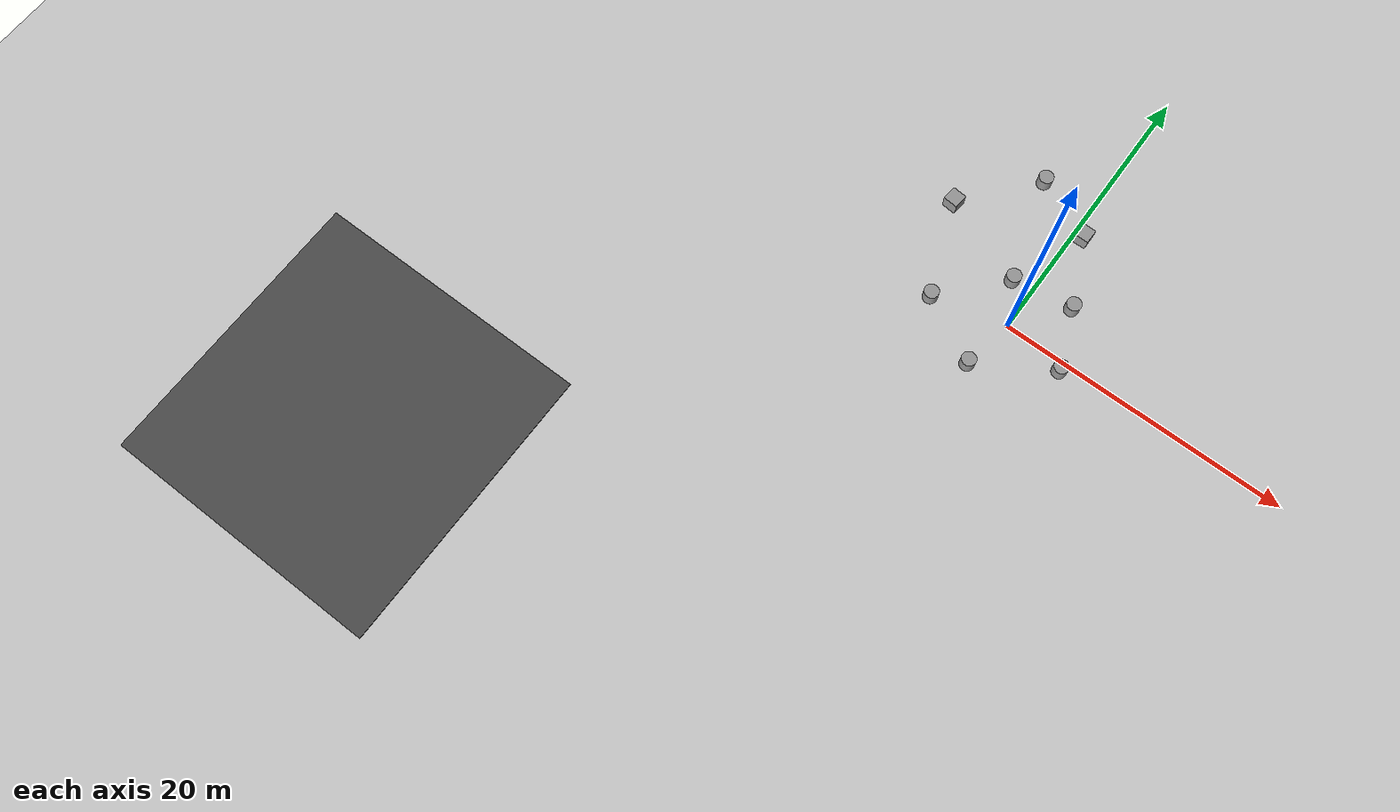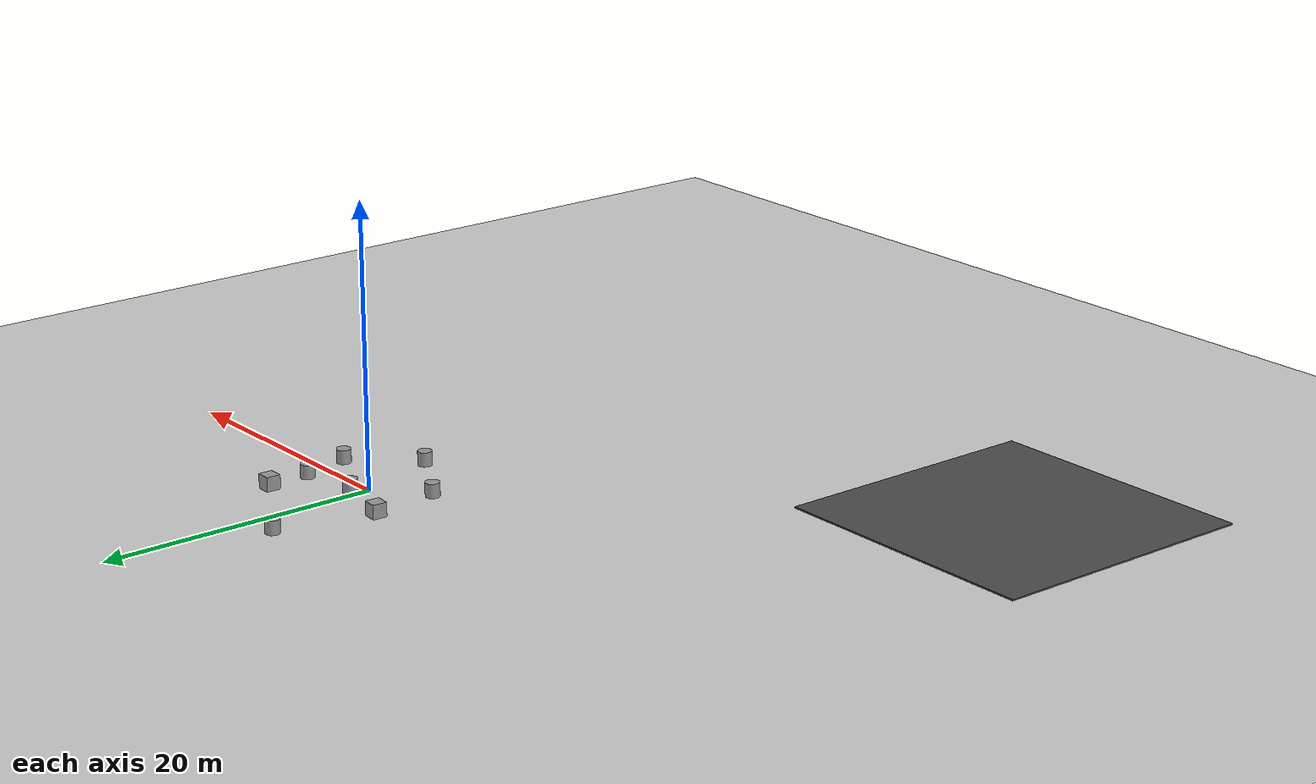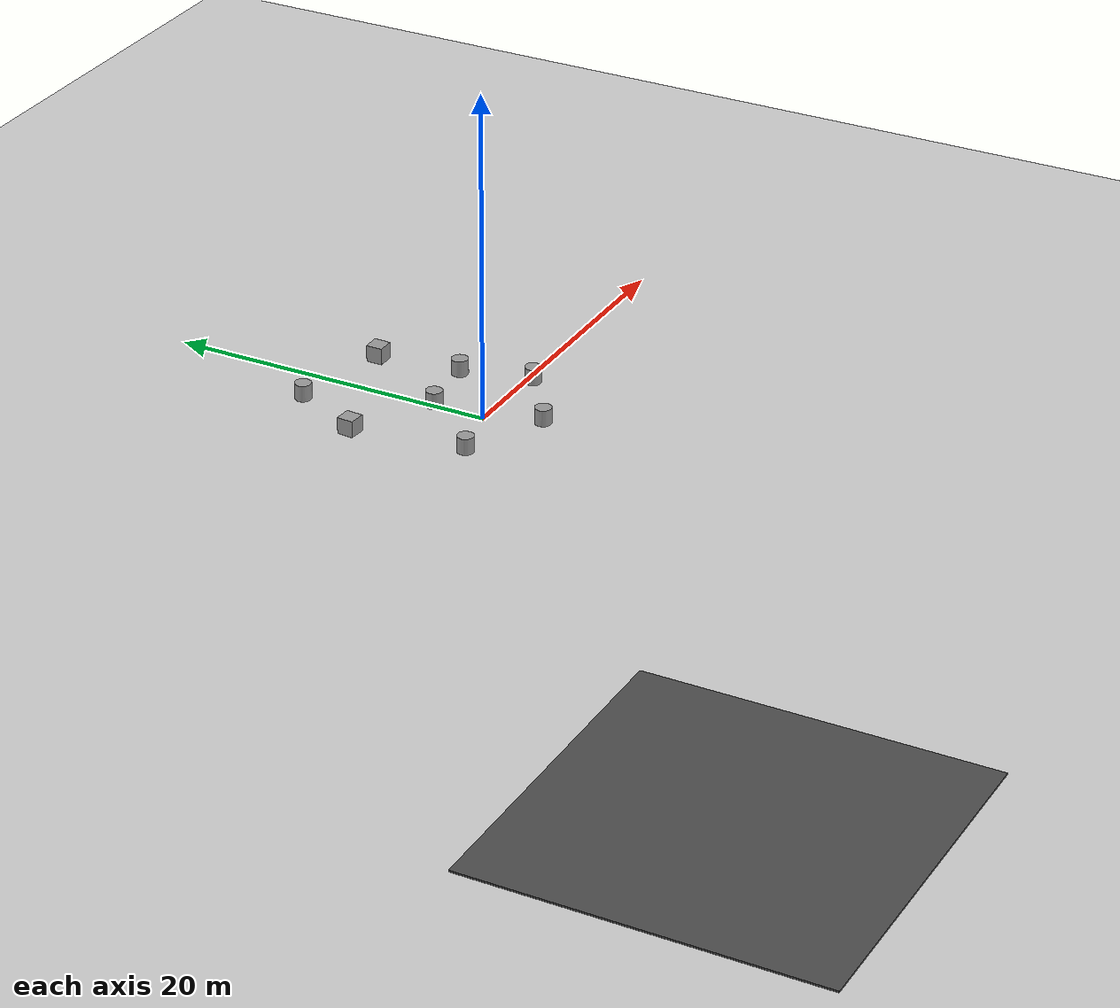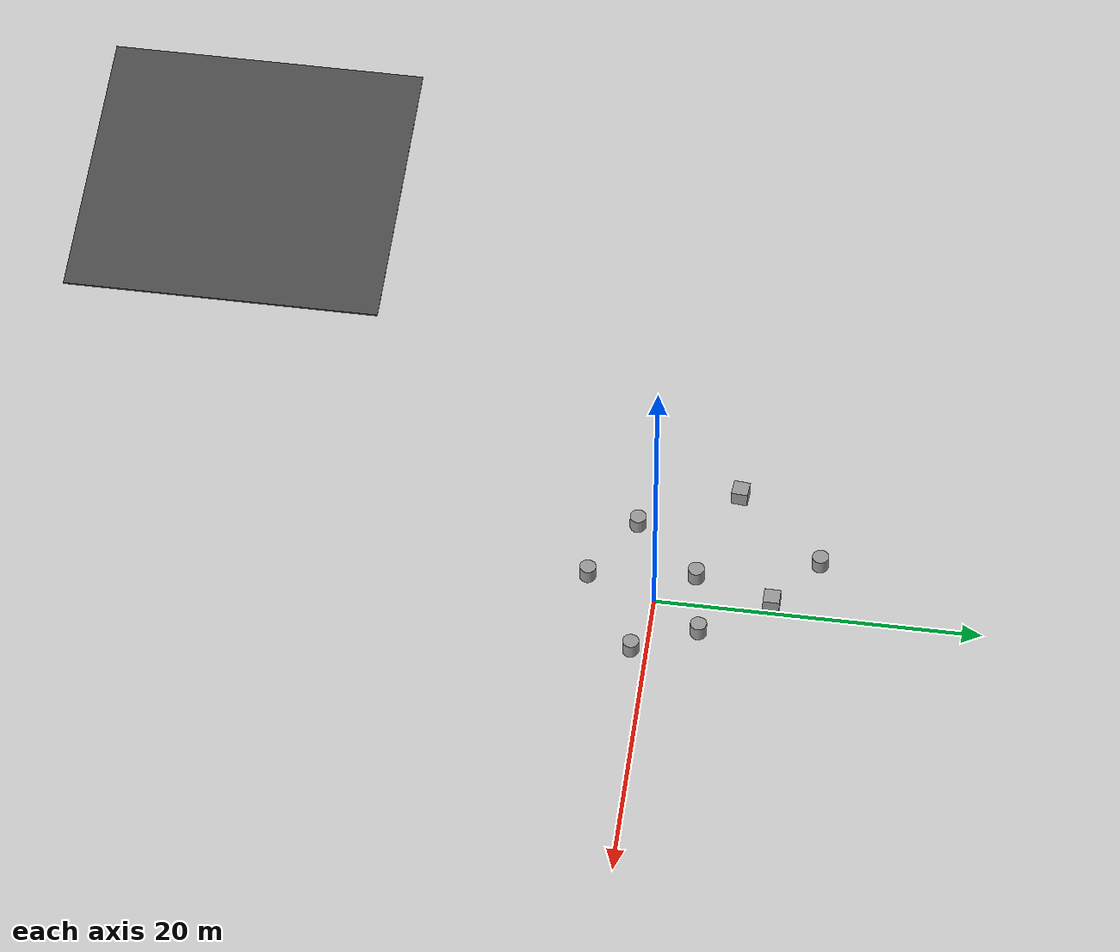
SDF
<sdf version="1.6">
 <world name="default">
  <model name="ground_plane">
   <static>1</static>
   <link name="link">
    <collision name="collision">
     <geometry><plane><normal>0 0 1</normal><size>100 100</size></plane></geometry>
     <surface><friction><ode><mu>100</mu><mu2>50</mu2></ode></friction></surface>
    </collision>
    <visual name="visual">
     <cast_shadows>0</cast_shadows>
     <geometry><plane><normal>0 0 1</normal><size>100 100</size></plane></geometry>
     <material>
      <script><uri>file://media/materials/scripts/gazebo.material</uri><name>Gazebo/Grey</name></script>
     </material>
    </visual>
   </link>
  </model>
  <light name="sun" type="directional">
   <pose>0 0 10 0 -0 0</pose>
   <diffuse>0.8 0.8 0.8 1</diffuse>
   <specular>0.2 0.2 0.2 1</specular>
   <attenuation>
    <range>1000</range>
    <constant>0.9</constant>
    <linear>0.01</linear>
    <quadratic>0.001</quadratic>
   </attenuation>
   <direction>-0.5 0.1 -0.9</direction>
  </light>
  <physics name="default_physics" default="0" type="ode">
   <ode>
    <solver>
     <type>quick</type>
     <iters>10</iters>
     <sor>1.3</sor>
     <use_dynamic_moi_rescaling>0</use_dynamic_moi_rescaling>
    </solver>
    <constraints>
     <cfm>0</cfm>
     <erp>0.2</erp>
     <contact_max_correcting_vel>100</contact_max_correcting_vel>
     <contact_surface_layer>0.001</contact_surface_layer>
    </constraints>
   </ode>
   <max_step_size>0.004</max_step_size>
   <real_time_factor>1</real_time_factor>
   <real_time_update_rate>250</real_time_update_rate>
  </physics>
  <scene><ambient>0.4 0.4 0.4 1</ambient><background>0.7 0.7 0.7 1</background><shadows>1</shadows></scene>
  <spherical_coordinates>
   <surface_model>EARTH_WGS84</surface_model>
   <latitude_deg>0</latitude_deg>
   <longitude_deg>0</longitude_deg>
   <elevation>0</elevation>
   <heading_deg>0</heading_deg>
  </spherical_coordinates>
  <model name="asphalt_plane">
   <static>1</static>
   <link name="link">
    <collision name="collision"><geometry><box><size>20 20 0.1</size></box></geometry></collision>
    <visual name="visual">
     <cast_shadows>0</cast_shadows>
     <geometry><box><size>20 20 0.1</size></box></geometry>
     <material>
      <script>
       <uri>model://asphalt_plane/materials/scripts</uri>
       <uri>model://asphalt_plane/materials/textures</uri>
       <name>vrc/asphalt</name>
      </script>
     </material>
    </visual>
    <velocity_decay><linear>0</linear><angular>0</angular></velocity_decay>
   </link>
   <pose>-30 -30 0 0 -0 0</pose>
  </model>
  <model name="asphalt_plane">
   <static>1</static>
   <link name="link">
    <collision name="collision"><geometry><box><size>20 20 0.1</size></box></geometry></collision>
    <visual name="visual">
     <cast_shadows>0</cast_shadows>
     <geometry><box><size>20 20 0.1</size></box></geometry>
     <material>
      <script>
       <uri>model://asphalt_plane/materials/scripts</uri>
       <uri>model://asphalt_plane/materials/textures</uri>
       <name>vrc/asphalt</name>
      </script>
     </material>
    </visual>
    <velocity_decay><linear>0</linear><angular>0</angular></velocity_decay>
   </link>
   <pose>-30 -30 0 0 -0 0</pose>
  </model>
  <model name="asphalt_plane">
   <static>1</static>
   <link name="link">
    <collision name="collision"><geometry><box><size>20 20 0.1</size></box></geometry></collision>
    <visual name="visual">
     <cast_shadows>0</cast_shadows>
     <geometry><box><size>20 20 0.1</size></box></geometry>
     <material>
      <script>
       <uri>model://asphalt_plane/materials/scripts</uri>
       <uri>model://asphalt_plane/materials/textures</uri>
       <name>vrc/asphalt</name>
      </script>
     </material>
    </visual>
    <velocity_decay><linear>0</linear><angular>0</angular></velocity_decay>
   </link>
   <pose>-30 -30 0 0 -0 0</pose>
  </model>
  <model name="asphalt_plane">
   <static>1</static>
   <link name="link">
    <collision name="collision"><geometry><box><size>20 20 0.1</size></box></geometry></collision>
    <visual name="visual">
     <cast_shadows>0</cast_shadows>
     <geometry><box><size>20 20 0.1</size></box></geometry>
     <material>
      <script>
       <uri>model://asphalt_plane/materials/scripts</uri>
       <uri>model://asphalt_plane/materials/textures</uri>
       <name>vrc/asphalt</name>
      </script>
     </material>
    </visual>
    <velocity_decay><linear>0</linear><angular>0</angular></velocity_decay>
   </link>
   <pose>-30 -30 0 0 -0 0</pose>
  </model>
  <model name="asphalt_plane">
   <static>1</static>
   <link name="link">
    <collision name="collision"><geometry><box><size>20 20 0.1</size></box></geometry></collision>
    <visual name="visual">
     <cast_shadows>0</cast_shadows>
     <geometry><box><size>20 20 0.1</size></box></geometry>
     <material>
      <script>
       <uri>model://asphalt_plane/materials/scripts</uri>
       <uri>model://asphalt_plane/materials/textures</uri>
       <name>vrc/asphalt</name>
      </script>
     </material>
    </visual>
    <velocity_decay><linear>0</linear><angular>0</angular></velocity_decay>
   </link>
   <pose>-30 -30 0 0 -0 0</pose>
  </model>
  <model name="asphalt_plane">
   <static>1</static>
   <link name="link">
    <collision name="collision"><geometry><box><size>20 20 0.1</size></box></geometry></collision>
    <visual name="visual">
     <cast_shadows>0</cast_shadows>
     <geometry><box><size>20 20 0.1</size></box></geometry>
     <material>
      <script>
       <uri>model://asphalt_plane/materials/scripts</uri>
       <uri>model://asphalt_plane/materials/textures</uri>
       <name>vrc/asphalt</name>
      </script>
     </material>
    </visual>
    <velocity_decay><linear>0</linear><angular>0</angular></velocity_decay>
   </link>
   <pose>-30 -30 0 0 -0 0</pose>
  </model>
  <model name="asphalt_plane">
   <static>1</static>
   <link name="link">
    <collision name="collision"><geometry><box><size>20 20 0.1</size></box></geometry></collision>
    <visual name="visual">
     <cast_shadows>0</cast_shadows>
     <geometry><box><size>20 20 0.1</size></box></geometry>
     <material>
      <script>
       <uri>model://asphalt_plane/materials/scripts</uri>
       <uri>model://asphalt_plane/materials/textures</uri>
       <name>vrc/asphalt</name>
      </script>
     </material>
    </visual>
    <velocity_decay><linear>0</linear><angular>0</angular></velocity_decay>
   </link>
   <pose>-30 -30 0 0 -0 0</pose>
  </model>
  <model name="asphalt_plane">
   <static>1</static>
   <link name="link">
    <collision name="collision"><geometry><box><size>20 20 0.1</size></box></geometry></collision>
    <visual name="visual">
     <cast_shadows>0</cast_shadows>
     <geometry><box><size>20 20 0.1</size></box></geometry>
     <material>
      <script>
       <uri>model://asphalt_plane/materials/scripts</uri>
       <uri>model://asphalt_plane/materials/textures</uri>
       <name>vrc/asphalt</name>
      </script>
     </material>
    </visual>
    <velocity_decay><linear>0</linear><angular>0</angular></velocity_decay>
   </link>
   <pose>-30 -30 0 0 -0 0</pose>
  </model>
  <model name="asphalt_plane">
   <static>1</static>
   <link name="link">
    <collision name="collision"><geometry><box><size>20 20 0.1</size></box></geometry></collision>
    <visual name="visual">
     <cast_shadows>0</cast_shadows>
     <geometry><box><size>20 20 0.1</size></box></geometry>
     <material>
      <script>
       <uri>model://asphalt_plane/materials/scripts</uri>
       <uri>model://asphalt_plane/materials/textures</uri>
       <name>vrc/asphalt</name>
      </script>
     </material>
    </visual>
    <velocity_decay><linear>0</linear><angular>0</angular></velocity_decay>
   </link>
   <pose>-30 -30 0 0 -0 0</pose>
  </model>
  <model name="asphalt_plane">
   <static>1</static>
   <link name="link">
    <collision name="collision"><geometry><box><size>20 20 0.1</size></box></geometry></collision>
    <visual name="visual">
     <cast_shadows>0</cast_shadows>
     <geometry><box><size>20 20 0.1</size></box></geometry>
     <material>
      <script>
       <uri>model://asphalt_plane/materials/scripts</uri>
       <uri>model://asphalt_plane/materials/textures</uri>
       <name>vrc/asphalt</name>
      </script>
     </material>
    </visual>
    <velocity_decay><linear>0</linear><angular>0</angular></velocity_decay>
   </link>
   <pose>-30 -30 0 0 -0 0</pose>
  </model>
  <model name="asphalt_plane">
   <static>1</static>
   <link name="link">
    <collision name="collision"><geometry><box><size>20 20 0.1</size></box></geometry></collision>
    <visual name="visual">
     <cast_shadows>0</cast_shadows>
     <geometry><box><size>20 20 0.1</size></box></geometry>
     <material>
      <script>
       <uri>model://asphalt_plane/materials/scripts</uri>
       <uri>model://asphalt_plane/materials/textures</uri>
       <name>vrc/asphalt</name>
      </script>
     </material>
    </visual>
    <velocity_decay><linear>0</linear><angular>0</angular></velocity_decay>
   </link>
   <pose>-30 -30 0 0 -0 0</pose>
  </model>
  <model name="asphalt_plane">
   <static>1</static>
   <link name="link">
    <collision name="collision"><geometry><box><size>20 20 0.1</size></box></geometry></collision>
    <visual name="visual">
     <cast_shadows>0</cast_shadows>
     <geometry><box><size>20 20 0.1</size></box></geometry>
     <material>
      <script>
       <uri>model://asphalt_plane/materials/scripts</uri>
       <uri>model://asphalt_plane/materials/textures</uri>
       <name>vrc/asphalt</name>
      </script>
     </material>
    </visual>
    <velocity_decay><linear>0</linear><angular>0</angular></velocity_decay>
   </link>
   <pose>-30 -30 0 0 -0 0</pose>
  </model>
  <model name="asphalt_plane">
   <static>1</static>
   <link name="link">
    <collision name="collision"><geometry><box><size>20 20 0.1</size></box></geometry></collision>
    <visual name="visual">
     <cast_shadows>0</cast_shadows>
     <geometry><box><size>20 20 0.1</size></box></geometry>
     <material>
      <script>
       <uri>model://asphalt_plane/materials/scripts</uri>
       <uri>model://asphalt_plane/materials/textures</uri>
       <name>vrc/asphalt</name>
      </script>
     </material>
    </visual>
    <velocity_decay><linear>0</linear><angular>0</angular></velocity_decay>
   </link>
   <pose>-30 -30 0 0 -0 0</pose>
  </model>
  <model name="asphalt_plane">
   <static>1</static>
   <link name="link">
    <collision name="collision"><geometry><box><size>20 20 0.1</size></box></geometry></collision>
    <visual name="visual">
     <cast_shadows>0</cast_shadows>
     <geometry><box><size>20 20 0.1</size></box></geometry>
     <material>
      <script>
       <uri>model://asphalt_plane/materials/scripts</uri>
       <uri>model://asphalt_plane/materials/textures</uri>
       <name>vrc/asphalt</name>
      </script>
     </material>
    </visual>
    <velocity_decay><linear>0</linear><angular>0</angular></velocity_decay>
   </link>
   <pose>-30 -30 0 0 -0 0</pose>
  </model>
  <model name="asphalt_plane">
   <static>1</static>
   <link name="link">
    <collision name="collision"><geometry><box><size>20 20 0.1</size></box></geometry></collision>
    <visual name="visual">
     <cast_shadows>0</cast_shadows>
     <geometry><box><size>20 20 0.1</size></box></geometry>
     <material>
      <script>
       <uri>model://asphalt_plane/materials/scripts</uri>
       <uri>model://asphalt_plane/materials/textures</uri>
       <name>vrc/asphalt</name>
      </script>
     </material>
    </visual>
    <velocity_decay><linear>0</linear><angular>0</angular></velocity_decay>
   </link>
   <pose>-30 -30 0 0 -0 0</pose>
  </model>
  <model name="asphalt_plane">
   <static>1</static>
   <link name="link">
    <collision name="collision"><geometry><box><size>20 20 0.1</size></box></geometry></collision>
    <visual name="visual">
     <cast_shadows>0</cast_shadows>
     <geometry><box><size>20 20 0.1</size></box></geometry>
     <material>
      <script>
       <uri>model://asphalt_plane/materials/scripts</uri>
       <uri>model://asphalt_plane/materials/textures</uri>
       <name>vrc/asphalt</name>
      </script>
     </material>
    </visual>
    <velocity_decay><linear>0</linear><angular>0</angular></velocity_decay>
   </link>
   <pose>-30 -30 0 0 -0 0</pose>
  </model>
  <model name="asphalt_plane">
   <static>1</static>
   <link name="link">
    <collision name="collision"><geometry><box><size>20 20 0.1</size></box></geometry></collision>
    <visual name="visual">
     <cast_shadows>0</cast_shadows>
     <geometry><box><size>20 20 0.1</size></box></geometry>
     <material>
      <script>
       <uri>model://asphalt_plane/materials/scripts</uri>
       <uri>model://asphalt_plane/materials/textures</uri>
       <name>vrc/asphalt</name>
      </script>
     </material>
    </visual>
    <velocity_decay><linear>0</linear><angular>0</angular></velocity_decay>
   </link>
   <pose>-30 -30 0 0 -0 0</pose>
  </model>
  <model name="asphalt_plane">
   <static>1</static>
   <link name="link">
    <collision name="collision"><geometry><box><size>20 20 0.1</size></box></geometry></collision>
    <visual name="visual">
     <cast_shadows>0</cast_shadows>
     <geometry><box><size>20 20 0.1</size></box></geometry>
     <material>
      <script>
       <uri>model://asphalt_plane/materials/scripts</uri>
       <uri>model://asphalt_plane/materials/textures</uri>
       <name>vrc/asphalt</name>
      </script>
     </material>
    </visual>
    <velocity_decay><linear>0</linear><angular>0</angular></velocity_decay>
   </link>
   <pose>-30 -30 0 0 -0 0</pose>
  </model>
  <model name="asphalt_plane">
   <static>1</static>
   <link name="link">
    <collision name="collision"><geometry><box><size>20 20 0.1</size></box></geometry></collision>
    <visual name="visual">
     <cast_shadows>0</cast_shadows>
     <geometry><box><size>20 20 0.1</size></box></geometry>
     <material>
      <script>
       <uri>model://asphalt_plane/materials/scripts</uri>
       <uri>model://asphalt_plane/materials/textures</uri>
       <name>vrc/asphalt</name>
      </script>
     </material>
    </visual>
    <velocity_decay><linear>0</linear><angular>0</angular></velocity_decay>
   </link>
   <pose>-30 -30 0 0 -0 0</pose>
  </model>
  <model name="asphalt_plane">
   <static>1</static>
   <link name="link">
    <collision name="collision"><geometry><box><size>20 20 0.1</size></box></geometry></collision>
    <visual name="visual">
     <cast_shadows>0</cast_shadows>
     <geometry><box><size>20 20 0.1</size></box></geometry>
     <material>
      <script>
       <uri>model://asphalt_plane/materials/scripts</uri>
       <uri>model://asphalt_plane/materials/textures</uri>
       <name>vrc/asphalt</name>
      </script>
     </material>
    </visual>
    <velocity_decay><linear>0</linear><angular>0</angular></velocity_decay>
   </link>
   <pose>-30 -30 0 0 -0 0</pose>
  </model>
  <model name="asphalt_plane">
   <static>1</static>
   <link name="link">
    <collision name="collision"><geometry><box><size>20 20 0.1</size></box></geometry></collision>
    <visual name="visual">
     <cast_shadows>0</cast_shadows>
     <geometry><box><size>20 20 0.1</size></box></geometry>
     <material>
      <script>
       <uri>model://asphalt_plane/materials/scripts</uri>
       <uri>model://asphalt_plane/materials/textures</uri>
       <name>vrc/asphalt</name>
      </script>
     </material>
    </visual>
    <velocity_decay><linear>0</linear><angular>0</angular></velocity_decay>
   </link>
   <pose>-30 -30 0 0 -0 0</pose>
  </model>
  <model name="asphalt_plane">
   <static>1</static>
   <link name="link">
    <collision name="collision"><geometry><box><size>20 20 0.1</size></box></geometry></collision>
    <visual name="visual">
     <cast_shadows>0</cast_shadows>
     <geometry><box><size>20 20 0.1</size></box></geometry>
     <material>
      <script>
       <uri>model://asphalt_plane/materials/scripts</uri>
       <uri>model://asphalt_plane/materials/textures</uri>
       <name>vrc/asphalt</name>
      </script>
     </material>
    </visual>
    <velocity_decay><linear>0</linear><angular>0</angular></velocity_decay>
   </link>
   <pose>-30 -30 0 0 -0 0</pose>
  </model>
  <model name="asphalt_plane">
   <static>1</static>
   <link name="link">
    <collision name="collision"><geometry><box><size>20 20 0.1</size></box></geometry></collision>
    <visual name="visual">
     <cast_shadows>0</cast_shadows>
     <geometry><box><size>20 20 0.1</size></box></geometry>
     <material>
      <script>
       <uri>model://asphalt_plane/materials/scripts</uri>
       <uri>model://asphalt_plane/materials/textures</uri>
       <name>vrc/asphalt</name>
      </script>
     </material>
    </visual>
    <velocity_decay><linear>0</linear><angular>0</angular></velocity_decay>
   </link>
   <pose>-30 -30 0 0 -0 0</pose>
  </model>
  <model name="asphalt_plane">
   <static>1</static>
   <link name="link">
    <collision name="collision"><geometry><box><size>20 20 0.1</size></box></geometry></collision>
    <visual name="visual">
     <cast_shadows>0</cast_shadows>
     <geometry><box><size>20 20 0.1</size></box></geometry>
     <material>
      <script>
       <uri>model://asphalt_plane/materials/scripts</uri>
       <uri>model://asphalt_plane/materials/textures</uri>
       <name>vrc/asphalt</name>
      </script>
     </material>
    </visual>
    <velocity_decay><linear>0</linear><angular>0</angular></velocity_decay>
   </link>
   <pose>-30 -30 0 0 -0 0</pose>
  </model>
  <model name="asphalt_plane">
   <static>1</static>
   <link name="link">
    <collision name="collision"><geometry><box><size>20 20 0.1</size></box></geometry></collision>
    <visual name="visual">
     <cast_shadows>0</cast_shadows>
     <geometry><box><size>20 20 0.1</size></box></geometry>
     <material>
      <script>
       <uri>model://asphalt_plane/materials/scripts</uri>
       <uri>model://asphalt_plane/materials/textures</uri>
       <name>vrc/asphalt</name>
      </script>
     </material>
    </visual>
    <velocity_decay><linear>0</linear><angular>0</angular></velocity_decay>
   </link>
   <pose>-30 -30 0 0 -0 0</pose>
  </model>
  <model name="asphalt_plane">
   <static>1</static>
   <link name="link">
    <collision name="collision"><geometry><box><size>20 20 0.1</size></box></geometry></collision>
    <visual name="visual">
     <cast_shadows>0</cast_shadows>
     <geometry><box><size>20 20 0.1</size></box></geometry>
     <material>
      <script>
       <uri>model://asphalt_plane/materials/scripts</uri>
       <uri>model://asphalt_plane/materials/textures</uri>
       <name>vrc/asphalt</name>
      </script>
     </material>
    </visual>
    <velocity_decay><linear>0</linear><angular>0</angular></velocity_decay>
   </link>
   <pose>-30 -30 0 0 -0 0</pose>
  </model>
  <model name="asphalt_plane">
   <static>1</static>
   <link name="link">
    <collision name="collision"><geometry><box><size>20 20 0.1</size></box></geometry></collision>
    <visual name="visual">
     <cast_shadows>0</cast_shadows>
     <geometry><box><size>20 20 0.1</size></box></geometry>
     <material>
      <script>
       <uri>model://asphalt_plane/materials/scripts</uri>
       <uri>model://asphalt_plane/materials/textures</uri>
       <name>vrc/asphalt</name>
      </script>
     </material>
    </visual>
    <velocity_decay><linear>0</linear><angular>0</angular></velocity_decay>
   </link>
   <pose>-30 -30 0 0 -0 0</pose>
  </model>
  <model name="asphalt_plane">
   <static>1</static>
   <link name="link">
    <collision name="collision"><geometry><box><size>20 20 0.1</size></box></geometry></collision>
    <visual name="visual">
     <cast_shadows>0</cast_shadows>
     <geometry><box><size>20 20 0.1</size></box></geometry>
     <material>
      <script>
       <uri>model://asphalt_plane/materials/scripts</uri>
       <uri>model://asphalt_plane/materials/textures</uri>
       <name>vrc/asphalt</name>
      </script>
     </material>
    </visual>
    <velocity_decay><linear>0</linear><angular>0</angular></velocity_decay>
   </link>
   <pose>-30 -30 0 0 -0 0</pose>
  </model>
  <model name="asphalt_plane">
   <static>1</static>
   <link name="link">
    <collision name="collision"><geometry><box><size>20 20 0.1</size></box></geometry></collision>
    <visual name="visual">
     <cast_shadows>0</cast_shadows>
     <geometry><box><size>20 20 0.1</size></box></geometry>
     <material>
      <script>
       <uri>model://asphalt_plane/materials/scripts</uri>
       <uri>model://asphalt_plane/materials/textures</uri>
       <name>vrc/asphalt</name>
      </script>
     </material>
    </visual>
    <velocity_decay><linear>0</linear><angular>0</angular></velocity_decay>
   </link>
   <pose>-30 -30 0 0 -0 0</pose>
  </model>
  <model name="asphalt_plane">
   <static>1</static>
   <link name="link">
    <collision name="collision"><geometry><box><size>20 20 0.1</size></box></geometry></collision>
    <visual name="visual">
     <cast_shadows>0</cast_shadows>
     <geometry><box><size>20 20 0.1</size></box></geometry>
     <material>
      <script>
       <uri>model://asphalt_plane/materials/scripts</uri>
       <uri>model://asphalt_plane/materials/textures</uri>
       <name>vrc/asphalt</name>
      </script>
     </material>
    </visual>
    <velocity_decay><linear>0</linear><angular>0</angular></velocity_decay>
   </link>
   <pose>-30 -30 0 0 -0 0</pose>
  </model>
  <model name="asphalt_plane">
   <static>1</static>
   <link name="link">
    <collision name="collision"><geometry><box><size>20 20 0.1</size></box></geometry></collision>
    <visual name="visual">
     <cast_shadows>0</cast_shadows>
     <geometry><box><size>20 20 0.1</size></box></geometry>
     <material>
      <script>
       <uri>model://asphalt_plane/materials/scripts</uri>
       <uri>model://asphalt_plane/materials/textures</uri>
       <name>vrc/asphalt</name>
      </script>
     </material>
    </visual>
    <velocity_decay><linear>0</linear><angular>0</angular></velocity_decay>
   </link>
   <pose>-30 -30 0 0 -0 0</pose>
  </model>
  <model name="asphalt_plane">
   <static>1</static>
   <link name="link">
    <collision name="collision"><geometry><box><size>20 20 0.1</size></box></geometry></collision>
    <visual name="visual">
     <cast_shadows>0</cast_shadows>
     <geometry><box><size>20 20 0.1</size></box></geometry>
     <material>
      <script>
       <uri>model://asphalt_plane/materials/scripts</uri>
       <uri>model://asphalt_plane/materials/textures</uri>
       <name>vrc/asphalt</name>
      </script>
     </material>
    </visual>
    <velocity_decay><linear>0</linear><angular>0</angular></velocity_decay>
   </link>
   <pose>-30 -30 0 0 -0 0</pose>
  </model>
  <model name="asphalt_plane">
   <static>1</static>
   <link name="link">
    <collision name="collision"><geometry><box><size>20 20 0.1</size></box></geometry></collision>
    <visual name="visual">
     <cast_shadows>0</cast_shadows>
     <geometry><box><size>20 20 0.1</size></box></geometry>
     <material>
      <script>
       <uri>model://asphalt_plane/materials/scripts</uri>
       <uri>model://asphalt_plane/materials/textures</uri>
       <name>vrc/asphalt</name>
      </script>
     </material>
    </visual>
    <velocity_decay><linear>0</linear><angular>0</angular></velocity_decay>
   </link>
   <pose>-30 -30 0 0 -0 0</pose>
  </model>
  <model name="asphalt_plane">
   <static>1</static>
   <link name="link">
    <collision name="collision"><geometry><box><size>20 20 0.1</size></box></geometry></collision>
    <visual name="visual">
     <cast_shadows>0</cast_shadows>
     <geometry><box><size>20 20 0.1</size></box></geometry>
     <material>
      <script>
       <uri>model://asphalt_plane/materials/scripts</uri>
       <uri>model://asphalt_plane/materials/textures</uri>
       <name>vrc/asphalt</name>
      </script>
     </material>
    </visual>
    <velocity_decay><linear>0</linear><angular>0</angular></velocity_decay>
   </link>
   <pose>-30 -30 0 0 -0 0</pose>
  </model>
  <model name="asphalt_plane">
   <static>1</static>
   <link name="link">
    <collision name="collision"><geometry><box><size>20 20 0.1</size></box></geometry></collision>
    <visual name="visual">
     <cast_shadows>0</cast_shadows>
     <geometry><box><size>20 20 0.1</size></box></geometry>
     <material>
      <script>
       <uri>model://asphalt_plane/materials/scripts</uri>
       <uri>model://asphalt_plane/materials/textures</uri>
       <name>vrc/asphalt</name>
      </script>
     </material>
    </visual>
    <velocity_decay><linear>0</linear><angular>0</angular></velocity_decay>
   </link>
   <pose>-30 -30 0 0 -0 0</pose>
  </model>
  <model name="asphalt_plane">
   <static>1</static>
   <link name="link">
    <collision name="collision"><geometry><box><size>20 20 0.1</size></box></geometry></collision>
    <visual name="visual">
     <cast_shadows>0</cast_shadows>
     <geometry><box><size>20 20 0.1</size></box></geometry>
     <material>
      <script>
       <uri>model://asphalt_plane/materials/scripts</uri>
       <uri>model://asphalt_plane/materials/textures</uri>
       <name>vrc/asphalt</name>
      </script>
     </material>
    </visual>
    <velocity_decay><linear>0</linear><angular>0</angular></velocity_decay>
   </link>
   <pose>-30 -30 0 0 -0 0</pose>
  </model>
  <model name="asphalt_plane">
   <static>1</static>
   <link name="link">
    <collision name="collision"><geometry><box><size>20 20 0.1</size></box></geometry></collision>
    <visual name="visual">
     <cast_shadows>0</cast_shadows>
     <geometry><box><size>20 20 0.1</size></box></geometry>
     <material>
      <script>
       <uri>model://asphalt_plane/materials/scripts</uri>
       <uri>model://asphalt_plane/materials/textures</uri>
       <name>vrc/asphalt</name>
      </script>
     </material>
    </visual>
    <velocity_decay><linear>0</linear><angular>0</angular></velocity_decay>
   </link>
   <pose>-30 -30 0 0 -0 0</pose>
  </model>
  <model name="asphalt_plane">
   <static>1</static>
   <link name="link">
    <collision name="collision"><geometry><box><size>20 20 0.1</size></box></geometry></collision>
    <visual name="visual">
     <cast_shadows>0</cast_shadows>
     <geometry><box><size>20 20 0.1</size></box></geometry>
     <material>
      <script>
       <uri>model://asphalt_plane/materials/scripts</uri>
       <uri>model://asphalt_plane/materials/textures</uri>
       <name>vrc/asphalt</name>
      </script>
     </material>
    </visual>
    <velocity_decay><linear>0</linear><angular>0</angular></velocity_decay>
   </link>
   <pose>-30 -30 0 0 -0 0</pose>
  </model>
  <model name="asphalt_plane">
   <static>1</static>
   <link name="link">
    <collision name="collision"><geometry><box><size>20 20 0.1</size></box></geometry></collision>
    <visual name="visual">
     <cast_shadows>0</cast_shadows>
     <geometry><box><size>20 20 0.1</size></box></geometry>
     <material>
      <script>
       <uri>model://asphalt_plane/materials/scripts</uri>
       <uri>model://asphalt_plane/materials/textures</uri>
       <name>vrc/asphalt</name>
      </script>
     </material>
    </visual>
    <velocity_decay><linear>0</linear><angular>0</angular></velocity_decay>
   </link>
   <pose>-30 -30 0 0 -0 0</pose>
  </model>
  <model name="asphalt_plane">
   <static>1</static>
   <link name="link">
    <collision name="collision"><geometry><box><size>20 20 0.1</size></box></geometry></collision>
    <visual name="visual">
     <cast_shadows>0</cast_shadows>
     <geometry><box><size>20 20 0.1</size></box></geometry>
     <material>
      <script>
       <uri>model://asphalt_plane/materials/scripts</uri>
       <uri>model://asphalt_plane/materials/textures</uri>
       <name>vrc/asphalt</name>
      </script>
     </material>
    </visual>
    <velocity_decay><linear>0</linear><angular>0</angular></velocity_decay>
   </link>
   <pose>-30 -30 0 0 -0 0</pose>
  </model>
  <model name="asphalt_plane">
   <static>1</static>
   <link name="link">
    <collision name="collision"><geometry><box><size>20 20 0.1</size></box></geometry></collision>
    <visual name="visual">
     <cast_shadows>0</cast_shadows>
     <geometry><box><size>20 20 0.1</size></box></geometry>
     <material>
      <script>
       <uri>model://asphalt_plane/materials/scripts</uri>
       <uri>model://asphalt_plane/materials/textures</uri>
       <name>vrc/asphalt</name>
      </script>
     </material>
    </visual>
    <velocity_decay><linear>0</linear><angular>0</angular></velocity_decay>
   </link>
   <pose>-30 -30 0 0 -0 0</pose>
  </model>
  <model name="asphalt_plane">
   <static>1</static>
   <link name="link">
    <collision name="collision"><geometry><box><size>20 20 0.1</size></box></geometry></collision>
    <visual name="visual">
     <cast_shadows>0</cast_shadows>
     <geometry><box><size>20 20 0.1</size></box></geometry>
     <material>
      <script>
       <uri>model://asphalt_plane/materials/scripts</uri>
       <uri>model://asphalt_plane/materials/textures</uri>
       <name>vrc/asphalt</name>
      </script>
     </material>
    </visual>
    <velocity_decay><linear>0</linear><angular>0</angular></velocity_decay>
   </link>
   <pose>-30 -30 0 0 -0 0</pose>
  </model>
  <model name="asphalt_plane">
   <static>1</static>
   <link name="link">
    <collision name="collision"><geometry><box><size>20 20 0.1</size></box></geometry></collision>
    <visual name="visual">
     <cast_shadows>0</cast_shadows>
     <geometry><box><size>20 20 0.1</size></box></geometry>
     <material>
      <script>
       <uri>model://asphalt_plane/materials/scripts</uri>
       <uri>model://asphalt_plane/materials/textures</uri>
       <name>vrc/asphalt</name>
      </script>
     </material>
    </visual>
    <velocity_decay><linear>0</linear><angular>0</angular></velocity_decay>
   </link>
   <pose>-30 -30 0 0 -0 0</pose>
  </model>
  <model name="asphalt_plane">
   <static>1</static>
   <link name="link">
    <collision name="collision"><geometry><box><size>20 20 0.1</size></box></geometry></collision>
    <visual name="visual">
     <cast_shadows>0</cast_shadows>
     <geometry><box><size>20 20 0.1</size></box></geometry>
     <material>
      <script>
       <uri>model://asphalt_plane/materials/scripts</uri>
       <uri>model://asphalt_plane/materials/textures</uri>
       <name>vrc/asphalt</name>
      </script>
     </material>
    </visual>
    <velocity_decay><linear>0</linear><angular>0</angular></velocity_decay>
   </link>
   <pose>-30 -30 0 0 -0 0</pose>
  </model>
  <model name="asphalt_plane">
   <static>1</static>
   <link name="link">
    <collision name="collision"><geometry><box><size>20 20 0.1</size></box></geometry></collision>
    <visual name="visual">
     <cast_shadows>0</cast_shadows>
     <geometry><box><size>20 20 0.1</size></box></geometry>
     <material>
      <script>
       <uri>model://asphalt_plane/materials/scripts</uri>
       <uri>model://asphalt_plane/materials/textures</uri>
       <name>vrc/asphalt</name>
      </script>
     </material>
    </visual>
    <velocity_decay><linear>0</linear><angular>0</angular></velocity_decay>
   </link>
   <pose>-30 -30 0 0 -0 0</pose>
  </model>
  <model name="asphalt_plane">
   <static>1</static>
   <link name="link">
    <collision name="collision"><geometry><box><size>20 20 0.1</size></box></geometry></collision>
    <visual name="visual">
     <cast_shadows>0</cast_shadows>
     <geometry><box><size>20 20 0.1</size></box></geometry>
     <material>
      <script>
       <uri>model://asphalt_plane/materials/scripts</uri>
       <uri>model://asphalt_plane/materials/textures</uri>
       <name>vrc/asphalt</name>
      </script>
     </material>
    </visual>
    <velocity_decay><linear>0</linear><angular>0</angular></velocity_decay>
   </link>
   <pose>-30 -30 0 0 -0 0</pose>
  </model>
  <model name="asphalt_plane">
   <static>1</static>
   <link name="link">
    <collision name="collision"><geometry><box><size>20 20 0.1</size></box></geometry></collision>
    <visual name="visual">
     <cast_shadows>0</cast_shadows>
     <geometry><box><size>20 20 0.1</size></box></geometry>
     <material>
      <script>
       <uri>model://asphalt_plane/materials/scripts</uri>
       <uri>model://asphalt_plane/materials/textures</uri>
       <name>vrc/asphalt</name>
      </script>
     </material>
    </visual>
    <velocity_decay><linear>0</linear><angular>0</angular></velocity_decay>
   </link>
   <pose>-30 -30 0 0 -0 0</pose>
  </model>
  <model name="asphalt_plane">
   <static>1</static>
   <link name="link">
    <collision name="collision"><geometry><box><size>20 20 0.1</size></box></geometry></collision>
    <visual name="visual">
     <cast_shadows>0</cast_shadows>
     <geometry><box><size>20 20 0.1</size></box></geometry>
     <material>
      <script>
       <uri>model://asphalt_plane/materials/scripts</uri>
       <uri>model://asphalt_plane/materials/textures</uri>
       <name>vrc/asphalt</name>
      </script>
     </material>
    </visual>
    <velocity_decay><linear>0</linear><angular>0</angular></velocity_decay>
   </link>
   <pose>-30 -30 0 0 -0 0</pose>
  </model>
  <model name="asphalt_plane">
   <static>1</static>
   <link name="link">
    <collision name="collision"><geometry><box><size>20 20 0.1</size></box></geometry></collision>
    <visual name="visual">
     <cast_shadows>0</cast_shadows>
     <geometry><box><size>20 20 0.1</size></box></geometry>
     <material>
      <script>
       <uri>model://asphalt_plane/materials/scripts</uri>
       <uri>model://asphalt_plane/materials/textures</uri>
       <name>vrc/asphalt</name>
      </script>
     </material>
    </visual>
    <velocity_decay><linear>0</linear><angular>0</angular></velocity_decay>
   </link>
   <pose>-30 -30 0 0 -0 0</pose>
  </model>
  <model name="asphalt_plane">
   <static>1</static>
   <link name="link">
    <collision name="collision"><geometry><box><size>20 20 0.1</size></box></geometry></collision>
    <visual name="visual">
     <cast_shadows>0</cast_shadows>
     <geometry><box><size>20 20 0.1</size></box></geometry>
     <material>
      <script>
       <uri>model://asphalt_plane/materials/scripts</uri>
       <uri>model://asphalt_plane/materials/textures</uri>
       <name>vrc/asphalt</name>
      </script>
     </material>
    </visual>
    <velocity_decay><linear>0</linear><angular>0</angular></velocity_decay>
   </link>
   <pose>-30 -30 0 0 -0 0</pose>
  </model>
  <model name="asphalt_plane">
   <static>1</static>
   <link name="link">
    <collision name="collision"><geometry><box><size>20 20 0.1</size></box></geometry></collision>
    <visual name="visual">
     <cast_shadows>0</cast_shadows>
     <geometry><box><size>20 20 0.1</size></box></geometry>
     <material>
      <script>
       <uri>model://asphalt_plane/materials/scripts</uri>
       <uri>model://asphalt_plane/materials/textures</uri>
       <name>vrc/asphalt</name>
      </script>
     </material>
    </visual>
    <velocity_decay><linear>0</linear><angular>0</angular></velocity_decay>
   </link>
   <pose>-30 -30 0 0 -0 0</pose>
  </model>
  <model name="asphalt_plane">
   <static>1</static>
   <link name="link">
    <collision name="collision"><geometry><box><size>20 20 0.1</size></box></geometry></collision>
    <visual name="visual">
     <cast_shadows>0</cast_shadows>
     <geometry><box><size>20 20 0.1</size></box></geometry>
     <material>
      <script>
       <uri>model://asphalt_plane/materials/scripts</uri>
       <uri>model://asphalt_plane/materials/textures</uri>
       <name>vrc/asphalt</name>
      </script>
     </material>
    </visual>
    <velocity_decay><linear>0</linear><angular>0</angular></velocity_decay>
   </link>
   <pose>-30 -30 0 0 -0 0</pose>
  </model>
  <model name="asphalt_plane">
   <static>1</static>
   <link name="link">
    <collision name="collision"><geometry><box><size>20 20 0.1</size></box></geometry></collision>
    <visual name="visual">
     <cast_shadows>0</cast_shadows>
     <geometry><box><size>20 20 0.1</size></box></geometry>
     <material>
      <script>
       <uri>model://asphalt_plane/materials/scripts</uri>
       <uri>model://asphalt_plane/materials/textures</uri>
       <name>vrc/asphalt</name>
      </script>
     </material>
    </visual>
    <velocity_decay><linear>0</linear><angular>0</angular></velocity_decay>
   </link>
   <pose>-30 -30 0 0 -0 0</pose>
  </model>
  <model name="asphalt_plane">
   <static>1</static>
   <link name="link">
    <collision name="collision"><geometry><box><size>20 20 0.1</size></box></geometry></collision>
    <visual name="visual">
     <cast_shadows>0</cast_shadows>
     <geometry><box><size>20 20 0.1</size></box></geometry>
     <material>
      <script>
       <uri>model://asphalt_plane/materials/scripts</uri>
       <uri>model://asphalt_plane/materials/textures</uri>
       <name>vrc/asphalt</name>
      </script>
     </material>
    </visual>
    <velocity_decay><linear>0</linear><angular>0</angular></velocity_decay>
   </link>
   <pose>-30 -30 0 0 -0 0</pose>
  </model>
  <model name="asphalt_plane">
   <static>1</static>
   <link name="link">
    <collision name="collision"><geometry><box><size>20 20 0.1</size></box></geometry></collision>
    <visual name="visual">
     <cast_shadows>0</cast_shadows>
     <geometry><box><size>20 20 0.1</size></box></geometry>
     <material>
      <script>
       <uri>model://asphalt_plane/materials/scripts</uri>
       <uri>model://asphalt_plane/materials/textures</uri>
       <name>vrc/asphalt</name>
      </script>
     </material>
    </visual>
    <velocity_decay><linear>0</linear><angular>0</angular></velocity_decay>
   </link>
   <pose>-30 -30 0 0 -0 0</pose>
  </model>
  <model name="asphalt_plane">
   <static>1</static>
   <link name="link">
    <collision name="collision"><geometry><box><size>20 20 0.1</size></box></geometry></collision>
    <visual name="visual">
     <cast_shadows>0</cast_shadows>
     <geometry><box><size>20 20 0.1</size></box></geometry>
     <material>
      <script>
       <uri>model://asphalt_plane/materials/scripts</uri>
       <uri>model://asphalt_plane/materials/textures</uri>
       <name>vrc/asphalt</name>
      </script>
     </material>
    </visual>
    <velocity_decay><linear>0</linear><angular>0</angular></velocity_decay>
   </link>
   <pose>-30 -30 0 0 -0 0</pose>
  </model>
  <model name="asphalt_plane">
   <static>1</static>
   <link name="link">
    <collision name="collision"><geometry><box><size>20 20 0.1</size></box></geometry></collision>
    <visual name="visual">
     <cast_shadows>0</cast_shadows>
     <geometry><box><size>20 20 0.1</size></box></geometry>
     <material>
      <script>
       <uri>model://asphalt_plane/materials/scripts</uri>
       <uri>model://asphalt_plane/materials/textures</uri>
       <name>vrc/asphalt</name>
      </script>
     </material>
    </visual>
    <velocity_decay><linear>0</linear><angular>0</angular></velocity_decay>
   </link>
   <pose>-30 -30 0 0 -0 0</pose>
  </model>
  <model name="asphalt_plane">
   <static>1</static>
   <link name="link">
    <collision name="collision"><geometry><box><size>20 20 0.1</size></box></geometry></collision>
    <visual name="visual">
     <cast_shadows>0</cast_shadows>
     <geometry><box><size>20 20 0.1</size></box></geometry>
     <material>
      <script>
       <uri>model://asphalt_plane/materials/scripts</uri>
       <uri>model://asphalt_plane/materials/textures</uri>
       <name>vrc/asphalt</name>
      </script>
     </material>
    </visual>
    <velocity_decay><linear>0</linear><angular>0</angular></velocity_decay>
   </link>
   <pose>-30 -30 0 0 -0 0</pose>
  </model>
  <model name="asphalt_plane">
   <static>1</static>
   <link name="link">
    <collision name="collision"><geometry><box><size>20 20 0.1</size></box></geometry></collision>
    <visual name="visual">
     <cast_shadows>0</cast_shadows>
     <geometry><box><size>20 20 0.1</size></box></geometry>
     <material>
      <script>
       <uri>model://asphalt_plane/materials/scripts</uri>
       <uri>model://asphalt_plane/materials/textures</uri>
       <name>vrc/asphalt</name>
      </script>
     </material>
    </visual>
    <velocity_decay><linear>0</linear><angular>0</angular></velocity_decay>
   </link>
   <pose>-30 -30 0 0 -0 0</pose>
  </model>
  <model name="asphalt_plane">
   <static>1</static>
   <link name="link">
    <collision name="collision"><geometry><box><size>20 20 0.1</size></box></geometry></collision>
    <visual name="visual">
     <cast_shadows>0</cast_shadows>
     <geometry><box><size>20 20 0.1</size></box></geometry>
     <material>
      <script>
       <uri>model://asphalt_plane/materials/scripts</uri>
       <uri>model://asphalt_plane/materials/textures</uri>
       <name>vrc/asphalt</name>
      </script>
     </material>
    </visual>
    <velocity_decay><linear>0</linear><angular>0</angular></velocity_decay>
   </link>
   <pose>-30 -30 0 0 -0 0</pose>
  </model>
  <model name="asphalt_plane">
   <static>1</static>
   <link name="link">
    <collision name="collision"><geometry><box><size>20 20 0.1</size></box></geometry></collision>
    <visual name="visual">
     <cast_shadows>0</cast_shadows>
     <geometry><box><size>20 20 0.1</size></box></geometry>
     <material>
      <script>
       <uri>model://asphalt_plane/materials/scripts</uri>
       <uri>model://asphalt_plane/materials/textures</uri>
       <name>vrc/asphalt</name>
      </script>
     </material>
    </visual>
    <velocity_decay><linear>0</linear><angular>0</angular></velocity_decay>
   </link>
   <pose>-30 -30 0 0 -0 0</pose>
  </model>
  <model name="asphalt_plane">
   <static>1</static>
   <link name="link">
    <collision name="collision"><geometry><box><size>20 20 0.1</size></box></geometry></collision>
    <visual name="visual">
     <cast_shadows>0</cast_shadows>
     <geometry><box><size>20 20 0.1</size></box></geometry>
     <material>
      <script>
       <uri>model://asphalt_plane/materials/scripts</uri>
       <uri>model://asphalt_plane/materials/textures</uri>
       <name>vrc/asphalt</name>
      </script>
     </material>
    </visual>
    <velocity_decay><linear>0</linear><angular>0</angular></velocity_decay>
   </link>
   <pose>-30 -30 0 0 -0 0</pose>
  </model>
  <model name="asphalt_plane">
   <static>1</static>
   <link name="link">
    <collision name="collision"><geometry><box><size>20 20 0.1</size></box></geometry></collision>
    <visual name="visual">
     <cast_shadows>0</cast_shadows>
     <geometry><box><size>20 20 0.1</size></box></geometry>
     <material>
      <script>
       <uri>model://asphalt_plane/materials/scripts</uri>
       <uri>model://asphalt_plane/materials/textures</uri>
       <name>vrc/asphalt</name>
      </script>
     </material>
    </visual>
    <velocity_decay><linear>0</linear><angular>0</angular></velocity_decay>
   </link>
   <pose>-30 -30 0 0 -0 0</pose>
  </model>
  <model name="asphalt_plane">
   <static>1</static>
   <link name="link">
    <collision name="collision"><geometry><box><size>20 20 0.1</size></box></geometry></collision>
    <visual name="visual">
     <cast_shadows>0</cast_shadows>
     <geometry><box><size>20 20 0.1</size></box></geometry>
     <material>
      <script>
       <uri>model://asphalt_plane/materials/scripts</uri>
       <uri>model://asphalt_plane/materials/textures</uri>
       <name>vrc/asphalt</name>
      </script>
     </material>
    </visual>
    <velocity_decay><linear>0</linear><angular>0</angular></velocity_decay>
   </link>
   <pose>-30 -30 0 0 -0 0</pose>
  </model>
  <model name="asphalt_plane">
   <static>1</static>
   <link name="link">
    <collision name="collision"><geometry><box><size>20 20 0.1</size></box></geometry></collision>
    <visual name="visual">
     <cast_shadows>0</cast_shadows>
     <geometry><box><size>20 20 0.1</size></box></geometry>
     <material>
      <script>
       <uri>model://asphalt_plane/materials/scripts</uri>
       <uri>model://asphalt_plane/materials/textures</uri>
       <name>vrc/asphalt</name>
      </script>
     </material>
    </visual>
    <velocity_decay><linear>0</linear><angular>0</angular></velocity_decay>
   </link>
   <pose>-30 -30 0 0 -0 0</pose>
  </model>
  <model name="asphalt_plane">
   <static>1</static>
   <link name="link">
    <collision name="collision"><geometry><box><size>20 20 0.1</size></box></geometry></collision>
    <visual name="visual">
     <cast_shadows>0</cast_shadows>
     <geometry><box><size>20 20 0.1</size></box></geometry>
     <material>
      <script>
       <uri>model://asphalt_plane/materials/scripts</uri>
       <uri>model://asphalt_plane/materials/textures</uri>
       <name>vrc/asphalt</name>
      </script>
     </material>
    </visual>
    <velocity_decay><linear>0</linear><angular>0</angular></velocity_decay>
   </link>
   <pose>-30 -30 0 0 -0 0</pose>
  </model>
  <model name="asphalt_plane">
   <static>1</static>
   <link name="link">
    <collision name="collision"><geometry><box><size>20 20 0.1</size></box></geometry></collision>
    <visual name="visual">
     <cast_shadows>0</cast_shadows>
     <geometry><box><size>20 20 0.1</size></box></geometry>
     <material>
      <script>
       <uri>model://asphalt_plane/materials/scripts</uri>
       <uri>model://asphalt_plane/materials/textures</uri>
       <name>vrc/asphalt</name>
      </script>
     </material>
    </visual>
    <velocity_decay><linear>0</linear><angular>0</angular></velocity_decay>
   </link>
   <pose>-30 -30 0 0 -0 0</pose>
  </model>
  <model name="asphalt_plane">
   <static>1</static>
   <link name="link">
    <collision name="collision"><geometry><box><size>20 20 0.1</size></box></geometry></collision>
    <visual name="visual">
     <cast_shadows>0</cast_shadows>
     <geometry><box><size>20 20 0.1</size></box></geometry>
     <material>
      <script>
       <uri>model://asphalt_plane/materials/scripts</uri>
       <uri>model://asphalt_plane/materials/textures</uri>
       <name>vrc/asphalt</name>
      </script>
     </material>
    </visual>
    <velocity_decay><linear>0</linear><angular>0</angular></velocity_decay>
   </link>
   <pose>-30 -30 0 0 -0 0</pose>
  </model>
  <model name="asphalt_plane">
   <static>1</static>
   <link name="link">
    <collision name="collision"><geometry><box><size>20 20 0.1</size></box></geometry></collision>
    <visual name="visual">
     <cast_shadows>0</cast_shadows>
     <geometry><box><size>20 20 0.1</size></box></geometry>
     <material>
      <script>
       <uri>model://asphalt_plane/materials/scripts</uri>
       <uri>model://asphalt_plane/materials/textures</uri>
       <name>vrc/asphalt</name>
      </script>
     </material>
    </visual>
    <velocity_decay><linear>0</linear><angular>0</angular></velocity_decay>
   </link>
   <pose>-30 -30 0 0 -0 0</pose>
  </model>
  <model name="asphalt_plane">
   <static>1</static>
   <link name="link">
    <collision name="collision"><geometry><box><size>20 20 0.1</size></box></geometry></collision>
    <visual name="visual">
     <cast_shadows>0</cast_shadows>
     <geometry><box><size>20 20 0.1</size></box></geometry>
     <material>
      <script>
       <uri>model://asphalt_plane/materials/scripts</uri>
       <uri>model://asphalt_plane/materials/textures</uri>
       <name>vrc/asphalt</name>
      </script>
     </material>
    </visual>
    <velocity_decay><linear>0</linear><angular>0</angular></velocity_decay>
   </link>
   <pose>-30 -30 0 0 -0 0</pose>
  </model>
  <model name="asphalt_plane">
   <static>1</static>
   <link name="link">
    <collision name="collision"><geometry><box><size>20 20 0.1</size></box></geometry></collision>
    <visual name="visual">
     <cast_shadows>0</cast_shadows>
     <geometry><box><size>20 20 0.1</size></box></geometry>
     <material>
      <script>
       <uri>model://asphalt_plane/materials/scripts</uri>
       <uri>model://asphalt_plane/materials/textures</uri>
       <name>vrc/asphalt</name>
      </script>
     </material>
    </visual>
    <velocity_decay><linear>0</linear><angular>0</angular></velocity_decay>
   </link>
   <pose>-30 -30 0 0 -0 0</pose>
  </model>
  <model name="asphalt_plane">
   <static>1</static>
   <link name="link">
    <collision name="collision"><geometry><box><size>20 20 0.1</size></box></geometry></collision>
    <visual name="visual">
     <cast_shadows>0</cast_shadows>
     <geometry><box><size>20 20 0.1</size></box></geometry>
     <material>
      <script>
       <uri>model://asphalt_plane/materials/scripts</uri>
       <uri>model://asphalt_plane/materials/textures</uri>
       <name>vrc/asphalt</name>
      </script>
     </material>
    </visual>
    <velocity_decay><linear>0</linear><angular>0</angular></velocity_decay>
   </link>
   <pose>-30 -30 0 0 -0 0</pose>
  </model>
  <model name="asphalt_plane">
   <static>1</static>
   <link name="link">
    <collision name="collision"><geometry><box><size>20 20 0.1</size></box></geometry></collision>
    <visual name="visual">
     <cast_shadows>0</cast_shadows>
     <geometry><box><size>20 20 0.1</size></box></geometry>
     <material>
      <script>
       <uri>model://asphalt_plane/materials/scripts</uri>
       <uri>model://asphalt_plane/materials/textures</uri>
       <name>vrc/asphalt</name>
      </script>
     </material>
    </visual>
    <velocity_decay><linear>0</linear><angular>0</angular></velocity_decay>
   </link>
   <pose>-30 -30 0 0 -0 0</pose>
  </model>
  <model name="asphalt_plane">
   <static>1</static>
   <link name="link">
    <collision name="collision"><geometry><box><size>20 20 0.1</size></box></geometry></collision>
    <visual name="visual">
     <cast_shadows>0</cast_shadows>
     <geometry><box><size>20 20 0.1</size></box></geometry>
     <material>
      <script>
       <uri>model://asphalt_plane/materials/scripts</uri>
       <uri>model://asphalt_plane/materials/textures</uri>
       <name>vrc/asphalt</name>
      </script>
     </material>
    </visual>
    <velocity_decay><linear>0</linear><angular>0</angular></velocity_decay>
   </link>
   <pose>-30 -30 0 0 -0 0</pose>
  </model>
  <model name="asphalt_plane">
   <static>1</static>
   <link name="link">
    <collision name="collision"><geometry><box><size>20 20 0.1</size></box></geometry></collision>
    <visual name="visual">
     <cast_shadows>0</cast_shadows>
     <geometry><box><size>20 20 0.1</size></box></geometry>
     <material>
      <script>
       <uri>model://asphalt_plane/materials/scripts</uri>
       <uri>model://asphalt_plane/materials/textures</uri>
       <name>vrc/asphalt</name>
      </script>
     </material>
    </visual>
    <velocity_decay><linear>0</linear><angular>0</angular></velocity_decay>
   </link>
   <pose>-30 -30 0 0 -0 0</pose>
  </model>
  <model name="asphalt_plane">
   <static>1</static>
   <link name="link">
    <collision name="collision"><geometry><box><size>20 20 0.1</size></box></geometry></collision>
    <visual name="visual">
     <cast_shadows>0</cast_shadows>
     <geometry><box><size>20 20 0.1</size></box></geometry>
     <material>
      <script>
       <uri>model://asphalt_plane/materials/scripts</uri>
       <uri>model://asphalt_plane/materials/textures</uri>
       <name>vrc/asphalt</name>
      </script>
     </material>
    </visual>
    <velocity_decay><linear>0</linear><angular>0</angular></velocity_decay>
   </link>
   <pose>-30 -30 0 0 -0 0</pose>
  </model>
  <model name="asphalt_plane">
   <static>1</static>
   <link name="link">
    <collision name="collision"><geometry><box><size>20 20 0.1</size></box></geometry></collision>
    <visual name="visual">
     <cast_shadows>0</cast_shadows>
     <geometry><box><size>20 20 0.1</size></box></geometry>
     <material>
      <script>
       <uri>model://asphalt_plane/materials/scripts</uri>
       <uri>model://asphalt_plane/materials/textures</uri>
       <name>vrc/asphalt</name>
      </script>
     </material>
    </visual>
    <velocity_decay><linear>0</linear><angular>0</angular></velocity_decay>
   </link>
   <pose>-30 -30 0 0 -0 0</pose>
  </model>
  <model name="asphalt_plane">
   <static>1</static>
   <link name="link">
    <collision name="collision"><geometry><box><size>20 20 0.1</size></box></geometry></collision>
    <visual name="visual">
     <cast_shadows>0</cast_shadows>
     <geometry><box><size>20 20 0.1</size></box></geometry>
     <material>
      <script>
       <uri>model://asphalt_plane/materials/scripts</uri>
       <uri>model://asphalt_plane/materials/textures</uri>
       <name>vrc/asphalt</name>
      </script>
     </material>
    </visual>
    <velocity_decay><linear>0</linear><angular>0</angular></velocity_decay>
   </link>
   <pose>-30 -30 0 0 -0 0</pose>
  </model>
  <model name="asphalt_plane">
   <static>1</static>
   <link name="link">
    <collision name="collision"><geometry><box><size>20 20 0.1</size></box></geometry></collision>
    <visual name="visual">
     <cast_shadows>0</cast_shadows>
     <geometry><box><size>20 20 0.1</size></box></geometry>
     <material>
      <script>
       <uri>model://asphalt_plane/materials/scripts</uri>
       <uri>model://asphalt_plane/materials/textures</uri>
       <name>vrc/asphalt</name>
      </script>
     </material>
    </visual>
    <velocity_decay><linear>0</linear><angular>0</angular></velocity_decay>
   </link>
   <pose>-30 -30 0 0 -0 0</pose>
  </model>
  <model name="asphalt_plane">
   <static>1</static>
   <link name="link">
    <collision name="collision"><geometry><box><size>20 20 0.1</size></box></geometry></collision>
    <visual name="visual">
     <cast_shadows>0</cast_shadows>
     <geometry><box><size>20 20 0.1</size></box></geometry>
     <material>
      <script>
       <uri>model://asphalt_plane/materials/scripts</uri>
       <uri>model://asphalt_plane/materials/textures</uri>
       <name>vrc/asphalt</name>
      </script>
     </material>
    </visual>
    <velocity_decay><linear>0</linear><angular>0</angular></velocity_decay>
   </link>
   <pose>-30 -30 0 0 -0 0</pose>
  </model>
  <model name="asphalt_plane">
   <static>1</static>
   <link name="link">
    <collision name="collision"><geometry><box><size>20 20 0.1</size></box></geometry></collision>
    <visual name="visual">
     <cast_shadows>0</cast_shadows>
     <geometry><box><size>20 20 0.1</size></box></geometry>
     <material>
      <script>
       <uri>model://asphalt_plane/materials/scripts</uri>
       <uri>model://asphalt_plane/materials/textures</uri>
       <name>vrc/asphalt</name>
      </script>
     </material>
    </visual>
    <velocity_decay><linear>0</linear><angular>0</angular></velocity_decay>
   </link>
   <pose>-30 -30 0 0 -0 0</pose>
  </model>
  <model name="asphalt_plane">
   <static>1</static>
   <link name="link">
    <collision name="collision"><geometry><box><size>20 20 0.1</size></box></geometry></collision>
    <visual name="visual">
     <cast_shadows>0</cast_shadows>
     <geometry><box><size>20 20 0.1</size></box></geometry>
     <material>
      <script>
       <uri>model://asphalt_plane/materials/scripts</uri>
       <uri>model://asphalt_plane/materials/textures</uri>
       <name>vrc/asphalt</name>
      </script>
     </material>
    </visual>
    <velocity_decay><linear>0</linear><angular>0</angular></velocity_decay>
   </link>
   <pose>-30 -30 0 0 -0 0</pose>
  </model>
  <model name="asphalt_plane">
   <static>1</static>
   <link name="link">
    <collision name="collision"><geometry><box><size>20 20 0.1</size></box></geometry></collision>
    <visual name="visual">
     <cast_shadows>0</cast_shadows>
     <geometry><box><size>20 20 0.1</size></box></geometry>
     <material>
      <script>
       <uri>model://asphalt_plane/materials/scripts</uri>
       <uri>model://asphalt_plane/materials/textures</uri>
       <name>vrc/asphalt</name>
      </script>
     </material>
    </visual>
    <velocity_decay><linear>0</linear><angular>0</angular></velocity_decay>
   </link>
   <pose>-30 -30 0 0 -0 0</pose>
  </model>
  <model name="asphalt_plane">
   <static>1</static>
   <link name="link">
    <collision name="collision"><geometry><box><size>20 20 0.1</size></box></geometry></collision>
    <visual name="visual">
     <cast_shadows>0</cast_shadows>
     <geometry><box><size>20 20 0.1</size></box></geometry>
     <material>
      <script>
       <uri>model://asphalt_plane/materials/scripts</uri>
       <uri>model://asphalt_plane/materials/textures</uri>
       <name>vrc/asphalt</name>
      </script>
     </material>
    </visual>
    <velocity_decay><linear>0</linear><angular>0</angular></velocity_decay>
   </link>
   <pose>-30 -30 0 0 -0 0</pose>
  </model>
  <model name="asphalt_plane">
   <static>1</static>
   <link name="link">
    <collision name="collision"><geometry><box><size>20 20 0.1</size></box></geometry></collision>
    <visual name="visual">
     <cast_shadows>0</cast_shadows>
     <geometry><box><size>20 20 0.1</size></box></geometry>
     <material>
      <script>
       <uri>model://asphalt_plane/materials/scripts</uri>
       <uri>model://asphalt_plane/materials/textures</uri>
       <name>vrc/asphalt</name>
      </script>
     </material>
    </visual>
    <velocity_decay><linear>0</linear><angular>0</angular></velocity_decay>
   </link>
   <pose>-30 -30 0 0 -0 0</pose>
  </model>
  <model name="asphalt_plane">
   <static>1</static>
   <link name="link">
    <collision name="collision"><geometry><box><size>20 20 0.1</size></box></geometry></collision>
    <visual name="visual">
     <cast_shadows>0</cast_shadows>
     <geometry><box><size>20 20 0.1</size></box></geometry>
     <material>
      <script>
       <uri>model://asphalt_plane/materials/scripts</uri>
       <uri>model://asphalt_plane/materials/textures</uri>
       <name>vrc/asphalt</name>
      </script>
     </material>
    </visual>
    <velocity_decay><linear>0</linear><angular>0</angular></velocity_decay>
   </link>
   <pose>-30 -30 0 0 -0 0</pose>
  </model>
  <model name="asphalt_plane">
   <static>1</static>
   <link name="link">
    <collision name="collision"><geometry><box><size>20 20 0.1</size></box></geometry></collision>
    <visual name="visual">
     <cast_shadows>0</cast_shadows>
     <geometry><box><size>20 20 0.1</size></box></geometry>
     <material>
      <script>
       <uri>model://asphalt_plane/materials/scripts</uri>
       <uri>model://asphalt_plane/materials/textures</uri>
       <name>vrc/asphalt</name>
      </script>
     </material>
    </visual>
    <velocity_decay><linear>0</linear><angular>0</angular></velocity_decay>
   </link>
   <pose>-30 -30 0 0 -0 0</pose>
  </model>
  <model name="asphalt_plane">
   <static>1</static>
   <link name="link">
    <collision name="collision"><geometry><box><size>20 20 0.1</size></box></geometry></collision>
    <visual name="visual">
     <cast_shadows>0</cast_shadows>
     <geometry><box><size>20 20 0.1</size></box></geometry>
     <material>
      <script>
       <uri>model://asphalt_plane/materials/scripts</uri>
       <uri>model://asphalt_plane/materials/textures</uri>
       <name>vrc/asphalt</name>
      </script>
     </material>
    </visual>
    <velocity_decay><linear>0</linear><angular>0</angular></velocity_decay>
   </link>
   <pose>-30 -30 0 0 -0 0</pose>
  </model>
  <model name="asphalt_plane">
   <static>1</static>
   <link name="link">
    <collision name="collision"><geometry><box><size>20 20 0.1</size></box></geometry></collision>
    <visual name="visual">
     <cast_shadows>0</cast_shadows>
     <geometry><box><size>20 20 0.1</size></box></geometry>
     <material>
      <script>
       <uri>model://asphalt_plane/materials/scripts</uri>
       <uri>model://asphalt_plane/materials/textures</uri>
       <name>vrc/asphalt</name>
      </script>
     </material>
    </visual>
    <velocity_decay><linear>0</linear><angular>0</angular></velocity_decay>
   </link>
   <pose>-30 -30 0 0 -0 0</pose>
  </model>
  <model name="asphalt_plane">
   <static>1</static>
   <link name="link">
    <collision name="collision"><geometry><box><size>20 20 0.1</size></box></geometry></collision>
    <visual name="visual">
     <cast_shadows>0</cast_shadows>
     <geometry><box><size>20 20 0.1</size></box></geometry>
     <material>
      <script>
       <uri>model://asphalt_plane/materials/scripts</uri>
       <uri>model://asphalt_plane/materials/textures</uri>
       <name>vrc/asphalt</name>
      </script>
     </material>
    </visual>
    <velocity_decay><linear>0</linear><angular>0</angular></velocity_decay>
   </link>
   <pose>-30 -30 0 0 -0 0</pose>
  </model>
  <model name="asphalt_plane">
   <static>1</static>
   <link name="link">
    <collision name="collision"><geometry><box><size>20 20 0.1</size></box></geometry></collision>
    <visual name="visual">
     <cast_shadows>0</cast_shadows>
     <geometry><box><size>20 20 0.1</size></box></geometry>
     <material>
      <script>
       <uri>model://asphalt_plane/materials/scripts</uri>
       <uri>model://asphalt_plane/materials/textures</uri>
       <name>vrc/asphalt</name>
      </script>
     </material>
    </visual>
    <velocity_decay><linear>0</linear><angular>0</angular></velocity_decay>
   </link>
   <pose>-30 -30 0 0 -0 0</pose>
  </model>
  <model name="asphalt_plane">
   <static>1</static>
   <link name="link">
    <collision name="collision"><geometry><box><size>20 20 0.1</size></box></geometry></collision>
    <visual name="visual">
     <cast_shadows>0</cast_shadows>
     <geometry><box><size>20 20 0.1</size></box></geometry>
     <material>
      <script>
       <uri>model://asphalt_plane/materials/scripts</uri>
       <uri>model://asphalt_plane/materials/textures</uri>
       <name>vrc/asphalt</name>
      </script>
     </material>
    </visual>
    <velocity_decay><linear>0</linear><angular>0</angular></velocity_decay>
   </link>
   <pose>-30 -30 0 0 -0 0</pose>
  </model>
  <model name="asphalt_plane">
   <static>1</static>
   <link name="link">
    <collision name="collision"><geometry><box><size>20 20 0.1</size></box></geometry></collision>
    <visual name="visual">
     <cast_shadows>0</cast_shadows>
     <geometry><box><size>20 20 0.1</size></box></geometry>
     <material>
      <script>
       <uri>model://asphalt_plane/materials/scripts</uri>
       <uri>model://asphalt_plane/materials/textures</uri>
       <name>vrc/asphalt</name>
      </script>
     </material>
    </visual>
    <velocity_decay><linear>0</linear><angular>0</angular></velocity_decay>
   </link>
   <pose>-30 -30 0 0 -0 0</pose>
  </model>
  <model name="asphalt_plane">
   <static>1</static>
   <link name="link">
    <collision name="collision"><geometry><box><size>20 20 0.1</size></box></geometry></collision>
    <visual name="visual">
     <cast_shadows>0</cast_shadows>
     <geometry><box><size>20 20 0.1</size></box></geometry>
     <material>
      <script>
       <uri>model://asphalt_plane/materials/scripts</uri>
       <uri>model://asphalt_plane/materials/textures</uri>
       <name>vrc/asphalt</name>
      </script>
     </material>
    </visual>
    <velocity_decay><linear>0</linear><angular>0</angular></velocity_decay>
   </link>
   <pose>-30 -30 0 0 -0 0</pose>
  </model>
  <model name="asphalt_plane">
   <static>1</static>
   <link name="link">
    <collision name="collision"><geometry><box><size>20 20 0.1</size></box></geometry></collision>
    <visual name="visual">
     <cast_shadows>0</cast_shadows>
     <geometry><box><size>20 20 0.1</size></box></geometry>
     <material>
      <script>
       <uri>model://asphalt_plane/materials/scripts</uri>
       <uri>model://asphalt_plane/materials/textures</uri>
       <name>vrc/asphalt</name>
      </script>
     </material>
    </visual>
    <velocity_decay><linear>0</linear><angular>0</angular></velocity_decay>
   </link>
   <pose>-30 -30 0 0 -0 0</pose>
  </model>
  <model name="asphalt_plane">
   <static>1</static>
   <link name="link">
    <collision name="collision"><geometry><box><size>20 20 0.1</size></box></geometry></collision>
    <visual name="visual">
     <cast_shadows>0</cast_shadows>
     <geometry><box><size>20 20 0.1</size></box></geometry>
     <material>
      <script>
       <uri>model://asphalt_plane/materials/scripts</uri>
       <uri>model://asphalt_plane/materials/textures</uri>
       <name>vrc/asphalt</name>
      </script>
     </material>
    </visual>
    <velocity_decay><linear>0</linear><angular>0</angular></velocity_decay>
   </link>
   <pose>-30 -30 0 0 -0 0</pose>
  </model>
  <model name="asphalt_plane">
   <static>1</static>
   <link name="link">
    <collision name="collision"><geometry><box><size>20 20 0.1</size></box></geometry></collision>
    <visual name="visual">
     <cast_shadows>0</cast_shadows>
     <geometry><box><size>20 20 0.1</size></box></geometry>
     <material>
      <script>
       <uri>model://asphalt_plane/materials/scripts</uri>
       <uri>model://asphalt_plane/materials/textures</uri>
       <name>vrc/asphalt</name>
      </script>
     </material>
    </visual>
    <velocity_decay><linear>0</linear><angular>0</angular></velocity_decay>
   </link>
   <pose>-30 -30 0 0 -0 0</pose>
  </model>
  <model name="asphalt_plane">
   <static>1</static>
   <link name="link">
    <collision name="collision"><geometry><box><size>20 20 0.1</size></box></geometry></collision>
    <visual name="visual">
     <cast_shadows>0</cast_shadows>
     <geometry><box><size>20 20 0.1</size></box></geometry>
     <material>
      <script>
       <uri>model://asphalt_plane/materials/scripts</uri>
       <uri>model://asphalt_plane/materials/textures</uri>
       <name>vrc/asphalt</name>
      </script>
     </material>
    </visual>
    <velocity_decay><linear>0</linear><angular>0</angular></velocity_decay>
   </link>
   <pose>-30 -30 0 0 -0 0</pose>
  </model>
  <model name="asphalt_plane">
   <static>1</static>
   <link name="link">
    <collision name="collision"><geometry><box><size>20 20 0.1</size></box></geometry></collision>
    <visual name="visual">
     <cast_shadows>0</cast_shadows>
     <geometry><box><size>20 20 0.1</size></box></geometry>
     <material>
      <script>
       <uri>model://asphalt_plane/materials/scripts</uri>
       <uri>model://asphalt_plane/materials/textures</uri>
       <name>vrc/asphalt</name>
      </script>
     </material>
    </visual>
    <velocity_decay><linear>0</linear><angular>0</angular></velocity_decay>
   </link>
   <pose>-30 -30 0 0 -0 0</pose>
  </model>
  <model name="asphalt_plane">
   <static>1</static>
   <link name="link">
    <collision name="collision"><geometry><box><size>20 20 0.1</size></box></geometry></collision>
    <visual name="visual">
     <cast_shadows>0</cast_shadows>
     <geometry><box><size>20 20 0.1</size></box></geometry>
     <material>
      <script>
       <uri>model://asphalt_plane/materials/scripts</uri>
       <uri>model://asphalt_plane/materials/textures</uri>
       <name>vrc/asphalt</name>
      </script>
     </material>
    </visual>
    <velocity_decay><linear>0</linear><angular>0</angular></velocity_decay>
   </link>
   <pose>-30 -30 0 0 -0 0</pose>
  </model>
  <model name="asphalt_plane">
   <static>1</static>
   <link name="link">
    <collision name="collision"><geometry><box><size>20 20 0.1</size></box></geometry></collision>
    <visual name="visual">
     <cast_shadows>0</cast_shadows>
     <geometry><box><size>20 20 0.1</size></box></geometry>
     <material>
      <script>
       <uri>model://asphalt_plane/materials/scripts</uri>
       <uri>model://asphalt_plane/materials/textures</uri>
       <name>vrc/asphalt</name>
      </script>
     </material>
    </visual>
    <velocity_decay><linear>0</linear><angular>0</angular></velocity_decay>
   </link>
   <pose>-30 -30 0 0 -0 0</pose>
  </model>
  <model name="asphalt_plane">
   <static>1</static>
   <link name="link">
    <collision name="collision"><geometry><box><size>20 20 0.1</size></box></geometry></collision>
    <visual name="visual">
     <cast_shadows>0</cast_shadows>
     <geometry><box><size>20 20 0.1</size></box></geometry>
     <material>
      <script>
       <uri>model://asphalt_plane/materials/scripts</uri>
       <uri>model://asphalt_plane/materials/textures</uri>
       <name>vrc/asphalt</name>
      </script>
     </material>
    </visual>
    <velocity_decay><linear>0</linear><angular>0</angular></velocity_decay>
   </link>
   <pose>-30 -30 0 0 -0 0</pose>
  </model>
  <model name="asphalt_plane">
   <static>1</static>
   <link name="link">
    <collision name="collision"><geometry><box><size>20 20 0.1</size></box></geometry></collision>
    <visual name="visual">
     <cast_shadows>0</cast_shadows>
     <geometry><box><size>20 20 0.1</size></box></geometry>
     <material>
      <script>
       <uri>model://asphalt_plane/materials/scripts</uri>
       <uri>model://asphalt_plane/materials/textures</uri>
       <name>vrc/asphalt</name>
      </script>
     </material>
    </visual>
    <velocity_decay><linear>0</linear><angular>0</angular></velocity_decay>
   </link>
   <pose>-30 -30 0 0 -0 0</pose>
  </model>
  <model name="asphalt_plane">
   <static>1</static>
   <link name="link">
    <collision name="collision"><geometry><box><size>20 20 0.1</size></box></geometry></collision>
    <visual name="visual">
     <cast_shadows>0</cast_shadows>
     <geometry><box><size>20 20 0.1</size></box></geometry>
     <material>
      <script>
       <uri>model://asphalt_plane/materials/scripts</uri>
       <uri>model://asphalt_plane/materials/textures</uri>
       <name>vrc/asphalt</name>
      </script>
     </material>
    </visual>
    <velocity_decay><linear>0</linear><angular>0</angular></velocity_decay>
   </link>
   <pose>-30 -30 0 0 -0 0</pose>
  </model>
  <model name="asphalt_plane">
   <static>1</static>
   <link name="link">
    <collision name="collision"><geometry><box><size>20 20 0.1</size></box></geometry></collision>
    <visual name="visual">
     <cast_shadows>0</cast_shadows>
     <geometry><box><size>20 20 0.1</size></box></geometry>
     <material>
      <script>
       <uri>model://asphalt_plane/materials/scripts</uri>
       <uri>model://asphalt_plane/materials/textures</uri>
       <name>vrc/asphalt</name>
      </script>
     </material>
    </visual>
    <velocity_decay><linear>0</linear><angular>0</angular></velocity_decay>
   </link>
   <pose>-30 -30 0 0 -0 0</pose>
  </model>
  <model name="asphalt_plane">
   <static>1</static>
   <link name="link">
    <collision name="collision"><geometry><box><size>20 20 0.1</size></box></geometry></collision>
    <visual name="visual">
     <cast_shadows>0</cast_shadows>
     <geometry><box><size>20 20 0.1</size></box></geometry>
     <material>
      <script>
       <uri>model://asphalt_plane/materials/scripts</uri>
       <uri>model://asphalt_plane/materials/textures</uri>
       <name>vrc/asphalt</name>
      </script>
     </material>
    </visual>
    <velocity_decay><linear>0</linear><angular>0</angular></velocity_decay>
   </link>
   <pose>-30 -30 0 0 -0 0</pose>
  </model>
  <model name="asphalt_plane">
   <static>1</static>
   <link name="link">
    <collision name="collision"><geometry><box><size>20 20 0.1</size></box></geometry></collision>
    <visual name="visual">
     <cast_shadows>0</cast_shadows>
     <geometry><box><size>20 20 0.1</size></box></geometry>
     <material>
      <script>
       <uri>model://asphalt_plane/materials/scripts</uri>
       <uri>model://asphalt_plane/materials/textures</uri>
       <name>vrc/asphalt</name>
      </script>
     </material>
    </visual>
    <velocity_decay><linear>0</linear><angular>0</angular></velocity_decay>
   </link>
   <pose>-30 -30 0 0 -0 0</pose>
  </model>
  <model name="asphalt_plane">
   <static>1</static>
   <link name="link">
    <collision name="collision"><geometry><box><size>20 20 0.1</size></box></geometry></collision>
    <visual name="visual">
     <cast_shadows>0</cast_shadows>
     <geometry><box><size>20 20 0.1</size></box></geometry>
     <material>
      <script>
       <uri>model://asphalt_plane/materials/scripts</uri>
       <uri>model://asphalt_plane/materials/textures</uri>
       <name>vrc/asphalt</name>
      </script>
     </material>
    </visual>
    <velocity_decay><linear>0</linear><angular>0</angular></velocity_decay>
   </link>
   <pose>-30 -30 0 0 -0 0</pose>
  </model>
  <model name="asphalt_plane">
   <static>1</static>
   <link name="link">
    <collision name="collision"><geometry><box><size>20 20 0.1</size></box></geometry></collision>
    <visual name="visual">
     <cast_shadows>0</cast_shadows>
     <geometry><box><size>20 20 0.1</size></box></geometry>
     <material>
      <script>
       <uri>model://asphalt_plane/materials/scripts</uri>
       <uri>model://asphalt_plane/materials/textures</uri>
       <name>vrc/asphalt</name>
      </script>
     </material>
    </visual>
    <velocity_decay><linear>0</linear><angular>0</angular></velocity_decay>
   </link>
   <pose>-30 -30 0 0 -0 0</pose>
  </model>
  <model name="asphalt_plane">
   <static>1</static>
   <link name="link">
    <collision name="collision"><geometry><box><size>20 20 0.1</size></box></geometry></collision>
    <visual name="visual">
     <cast_shadows>0</cast_shadows>
     <geometry><box><size>20 20 0.1</size></box></geometry>
     <material>
      <script>
       <uri>model://asphalt_plane/materials/scripts</uri>
       <uri>model://asphalt_plane/materials/textures</uri>
       <name>vrc/asphalt</name>
      </script>
     </material>
    </visual>
    <velocity_decay><linear>0</linear><angular>0</angular></velocity_decay>
   </link>
   <pose>-30 -30 0 0 -0 0</pose>
  </model>
  <model name="asphalt_plane">
   <static>1</static>
   <link name="link">
    <collision name="collision"><geometry><box><size>20 20 0.1</size></box></geometry></collision>
    <visual name="visual">
     <cast_shadows>0</cast_shadows>
     <geometry><box><size>20 20 0.1</size></box></geometry>
     <material>
      <script>
       <uri>model://asphalt_plane/materials/scripts</uri>
       <uri>model://asphalt_plane/materials/textures</uri>
       <name>vrc/asphalt</name>
      </script>
     </material>
    </visual>
    <velocity_decay><linear>0</linear><angular>0</angular></velocity_decay>
   </link>
   <pose>-30 -30 0 0 -0 0</pose>
  </model>
  <model name="asphalt_plane">
   <static>1</static>
   <link name="link">
    <collision name="collision"><geometry><box><size>20 20 0.1</size></box></geometry></collision>
    <visual name="visual">
     <cast_shadows>0</cast_shadows>
     <geometry><box><size>20 20 0.1</size></box></geometry>
     <material>
      <script>
       <uri>model://asphalt_plane/materials/scripts</uri>
       <uri>model://asphalt_plane/materials/textures</uri>
       <name>vrc/asphalt</name>
      </script>
     </material>
    </visual>
    <velocity_decay><linear>0</linear><angular>0</angular></velocity_decay>
   </link>
   <pose>-30 -30 0 0 -0 0</pose>
  </model>
  <model name="asphalt_plane">
   <static>1</static>
   <link name="link">
    <collision name="collision"><geometry><box><size>20 20 0.1</size></box></geometry></collision>
    <visual name="visual">
     <cast_shadows>0</cast_shadows>
     <geometry><box><size>20 20 0.1</size></box></geometry>
     <material>
      <script>
       <uri>model://asphalt_plane/materials/scripts</uri>
       <uri>model://asphalt_plane/materials/textures</uri>
       <name>vrc/asphalt</name>
      </script>
     </material>
    </visual>
    <velocity_decay><linear>0</linear><angular>0</angular></velocity_decay>
   </link>
   <pose>-30 -30 0 0 -0 0</pose>
  </model>
  <model name="asphalt_plane">
   <static>1</static>
   <link name="link">
    <collision name="collision"><geometry><box><size>20 20 0.1</size></box></geometry></collision>
    <visual name="visual">
     <cast_shadows>0</cast_shadows>
     <geometry><box><size>20 20 0.1</size></box></geometry>
     <material>
      <script>
       <uri>model://asphalt_plane/materials/scripts</uri>
       <uri>model://asphalt_plane/materials/textures</uri>
       <name>vrc/asphalt</name>
      </script>
     </material>
    </visual>
    <velocity_decay><linear>0</linear><angular>0</angular></velocity_decay>
   </link>
   <pose>-30 -30 0 0 -0 0</pose>
  </model>
  <model name="asphalt_plane">
   <static>1</static>
   <link name="link">
    <collision name="collision"><geometry><box><size>20 20 0.1</size></box></geometry></collision>
    <visual name="visual">
     <cast_shadows>0</cast_shadows>
     <geometry><box><size>20 20 0.1</size></box></geometry>
     <material>
      <script>
       <uri>model://asphalt_plane/materials/scripts</uri>
       <uri>model://asphalt_plane/materials/textures</uri>
       <name>vrc/asphalt</name>
      </script>
     </material>
    </visual>
    <velocity_decay><linear>0</linear><angular>0</angular></velocity_decay>
   </link>
   <pose>-30 -30 0 0 -0 0</pose>
  </model>
  <model name="asphalt_plane">
   <static>1</static>
   <link name="link">
    <collision name="collision"><geometry><box><size>20 20 0.1</size></box></geometry></collision>
    <visual name="visual">
     <cast_shadows>0</cast_shadows>
     <geometry><box><size>20 20 0.1</size></box></geometry>
     <material>
      <script>
       <uri>model://asphalt_plane/materials/scripts</uri>
       <uri>model://asphalt_plane/materials/textures</uri>
       <name>vrc/asphalt</name>
      </script>
     </material>
    </visual>
    <velocity_decay><linear>0</linear><angular>0</angular></velocity_decay>
   </link>
   <pose>-30 -30 0 0 -0 0</pose>
  </model>
  <model name="asphalt_plane">
   <static>1</static>
   <link name="link">
    <collision name="collision"><geometry><box><size>20 20 0.1</size></box></geometry></collision>
    <visual name="visual">
     <cast_shadows>0</cast_shadows>
     <geometry><box><size>20 20 0.1</size></box></geometry>
     <material>
      <script>
       <uri>model://asphalt_plane/materials/scripts</uri>
       <uri>model://asphalt_plane/materials/textures</uri>
       <name>vrc/asphalt</name>
      </script>
     </material>
    </visual>
    <velocity_decay><linear>0</linear><angular>0</angular></velocity_decay>
   </link>
   <pose>-30 -30 0 0 -0 0</pose>
  </model>
  <model name="asphalt_plane">
   <static>1</static>
   <link name="link">
    <collision name="collision"><geometry><box><size>20 20 0.1</size></box></geometry></collision>
    <visual name="visual">
     <cast_shadows>0</cast_shadows>
     <geometry><box><size>20 20 0.1</size></box></geometry>
     <material>
      <script>
       <uri>model://asphalt_plane/materials/scripts</uri>
       <uri>model://asphalt_plane/materials/textures</uri>
       <name>vrc/asphalt</name>
      </script>
     </material>
    </visual>
    <velocity_decay><linear>0</linear><angular>0</angular></velocity_decay>
   </link>
   <pose>-30 -30 0 0 -0 0</pose>
  </model>
  <model name="asphalt_plane">
   <static>1</static>
   <link name="link">
    <collision name="collision"><geometry><box><size>20 20 0.1</size></box></geometry></collision>
    <visual name="visual">
     <cast_shadows>0</cast_shadows>
     <geometry><box><size>20 20 0.1</size></box></geometry>
     <material>
      <script>
       <uri>model://asphalt_plane/materials/scripts</uri>
       <uri>model://asphalt_plane/materials/textures</uri>
       <name>vrc/asphalt</name>
      </script>
     </material>
    </visual>
    <velocity_decay><linear>0</linear><angular>0</angular></velocity_decay>
   </link>
   <pose>-30 -30 0 0 -0 0</pose>
  </model>
  <model name="asphalt_plane">
   <static>1</static>
   <link name="link">
    <collision name="collision"><geometry><box><size>20 20 0.1</size></box></geometry></collision>
    <visual name="visual">
     <cast_shadows>0</cast_shadows>
     <geometry><box><size>20 20 0.1</size></box></geometry>
     <material>
      <script>
       <uri>model://asphalt_plane/materials/scripts</uri>
       <uri>model://asphalt_plane/materials/textures</uri>
       <name>vrc/asphalt</name>
      </script>
     </material>
    </visual>
    <velocity_decay><linear>0</linear><angular>0</angular></velocity_decay>
   </link>
   <pose>-30 -30 0 0 -0 0</pose>
  </model>
  <model name="asphalt_plane">
   <static>1</static>
   <link name="link">
    <collision name="collision"><geometry><box><size>20 20 0.1</size></box></geometry></collision>
    <visual name="visual">
     <cast_shadows>0</cast_shadows>
     <geometry><box><size>20 20 0.1</size></box></geometry>
     <material>
      <script>
       <uri>model://asphalt_plane/materials/scripts</uri>
       <uri>model://asphalt_plane/materials/textures</uri>
       <name>vrc/asphalt</name>
      </script>
     </material>
    </visual>
    <velocity_decay><linear>0</linear><angular>0</angular></velocity_decay>
   </link>
   <pose>-30 -30 0 0 -0 0</pose>
  </model>
  <model name="asphalt_plane">
   <static>1</static>
   <link name="link">
    <collision name="collision"><geometry><box><size>20 20 0.1</size></box></geometry></collision>
    <visual name="visual">
     <cast_shadows>0</cast_shadows>
     <geometry><box><size>20 20 0.1</size></box></geometry>
     <material>
      <script>
       <uri>model://asphalt_plane/materials/scripts</uri>
       <uri>model://asphalt_plane/materials/textures</uri>
       <name>vrc/asphalt</name>
      </script>
     </material>
    </visual>
    <velocity_decay><linear>0</linear><angular>0</angular></velocity_decay>
   </link>
   <pose>-30 -30 0 0 -0 0</pose>
  </model>
  <model name="asphalt_plane">
   <static>1</static>
   <link name="link">
    <collision name="collision"><geometry><box><size>20 20 0.1</size></box></geometry></collision>
    <visual name="visual">
     <cast_shadows>0</cast_shadows>
     <geometry><box><size>20 20 0.1</size></box></geometry>
     <material>
      <script>
       <uri>model://asphalt_plane/materials/scripts</uri>
       <uri>model://asphalt_plane/materials/textures</uri>
       <name>vrc/asphalt</name>
      </script>
     </material>
    </visual>
    <velocity_decay><linear>0</linear><angular>0</angular></velocity_decay>
   </link>
   <pose>-30 -30 0 0 -0 0</pose>
  </model>
  <model name="asphalt_plane">
   <static>1</static>
   <link name="link">
    <collision name="collision"><geometry><box><size>20 20 0.1</size></box></geometry></collision>
    <visual name="visual">
     <cast_shadows>0</cast_shadows>
     <geometry><box><size>20 20 0.1</size></box></geometry>
     <material>
      <script>
       <uri>model://asphalt_plane/materials/scripts</uri>
       <uri>model://asphalt_plane/materials/textures</uri>
       <name>vrc/asphalt</name>
      </script>
     </material>
    </visual>
    <velocity_decay><linear>0</linear><angular>0</angular></velocity_decay>
   </link>
   <pose>-30 -30 0 0 -0 0</pose>
  </model>
  <model name="asphalt_plane">
   <static>1</static>
   <link name="link">
    <collision name="collision"><geometry><box><size>20 20 0.1</size></box></geometry></collision>
    <visual name="visual">
     <cast_shadows>0</cast_shadows>
     <geometry><box><size>20 20 0.1</size></box></geometry>
     <material>
      <script>
       <uri>model://asphalt_plane/materials/scripts</uri>
       <uri>model://asphalt_plane/materials/textures</uri>
       <name>vrc/asphalt</name>
      </script>
     </material>
    </visual>
    <velocity_decay><linear>0</linear><angular>0</angular></velocity_decay>
   </link>
   <pose>-30 -30 0 0 -0 0</pose>
  </model>
  <model name="asphalt_plane">
   <static>1</static>
   <link name="link">
    <collision name="collision"><geometry><box><size>20 20 0.1</size></box></geometry></collision>
    <visual name="visual">
     <cast_shadows>0</cast_shadows>
     <geometry><box><size>20 20 0.1</size></box></geometry>
     <material>
      <script>
       <uri>model://asphalt_plane/materials/scripts</uri>
       <uri>model://asphalt_plane/materials/textures</uri>
       <name>vrc/asphalt</name>
      </script>
     </material>
    </visual>
    <velocity_decay><linear>0</linear><angular>0</angular></velocity_decay>
   </link>
   <pose>-30 -30 0 0 -0 0</pose>
  </model>
  <model name="asphalt_plane">
   <static>1</static>
   <link name="link">
    <collision name="collision"><geometry><box><size>20 20 0.1</size></box></geometry></collision>
    <visual name="visual">
     <cast_shadows>0</cast_shadows>
     <geometry><box><size>20 20 0.1</size></box></geometry>
     <material>
      <script>
       <uri>model://asphalt_plane/materials/scripts</uri>
       <uri>model://asphalt_plane/materials/textures</uri>
       <name>vrc/asphalt</name>
      </script>
     </material>
    </visual>
    <velocity_decay><linear>0</linear><angular>0</angular></velocity_decay>
   </link>
   <pose>-30 -30 0 0 -0 0</pose>
  </model>
  <model name="asphalt_plane">
   <static>1</static>
   <link name="link">
    <collision name="collision"><geometry><box><size>20 20 0.1</size></box></geometry></collision>
    <visual name="visual">
     <cast_shadows>0</cast_shadows>
     <geometry><box><size>20 20 0.1</size></box></geometry>
     <material>
      <script>
       <uri>model://asphalt_plane/materials/scripts</uri>
       <uri>model://asphalt_plane/materials/textures</uri>
       <name>vrc/asphalt</name>
      </script>
     </material>
    </visual>
    <velocity_decay><linear>0</linear><angular>0</angular></velocity_decay>
   </link>
   <pose>-30 -30 0 0 -0 0</pose>
  </model>
  <model name="asphalt_plane">
   <static>1</static>
   <link name="link">
    <collision name="collision"><geometry><box><size>20 20 0.1</size></box></geometry></collision>
    <visual name="visual">
     <cast_shadows>0</cast_shadows>
     <geometry><box><size>20 20 0.1</size></box></geometry>
     <material>
      <script>
       <uri>model://asphalt_plane/materials/scripts</uri>
       <uri>model://asphalt_plane/materials/textures</uri>
       <name>vrc/asphalt</name>
      </script>
     </material>
    </visual>
    <velocity_decay><linear>0</linear><angular>0</angular></velocity_decay>
   </link>
   <pose>-30 -30 0 0 -0 0</pose>
  </model>
  <model name="asphalt_plane">
   <static>1</static>
   <link name="link">
    <collision name="collision"><geometry><box><size>20 20 0.1</size></box></geometry></collision>
    <visual name="visual">
     <cast_shadows>0</cast_shadows>
     <geometry><box><size>20 20 0.1</size></box></geometry>
     <material>
      <script>
       <uri>model://asphalt_plane/materials/scripts</uri>
       <uri>model://asphalt_plane/materials/textures</uri>
       <name>vrc/asphalt</name>
      </script>
     </material>
    </visual>
    <velocity_decay><linear>0</linear><angular>0</angular></velocity_decay>
   </link>
   <pose>-30 -30 0 0 -0 0</pose>
  </model>
  <model name="asphalt_plane">
   <static>1</static>
   <link name="link">
    <collision name="collision"><geometry><box><size>20 20 0.1</size></box></geometry></collision>
    <visual name="visual">
     <cast_shadows>0</cast_shadows>
     <geometry><box><size>20 20 0.1</size></box></geometry>
     <material>
      <script>
       <uri>model://asphalt_plane/materials/scripts</uri>
       <uri>model://asphalt_plane/materials/textures</uri>
       <name>vrc/asphalt</name>
      </script>
     </material>
    </visual>
    <velocity_decay><linear>0</linear><angular>0</angular></velocity_decay>
   </link>
   <pose>-30 -30 0 0 -0 0</pose>
  </model>
  <model name="asphalt_plane">
   <static>1</static>
   <link name="link">
    <collision name="collision"><geometry><box><size>20 20 0.1</size></box></geometry></collision>
    <visual name="visual">
     <cast_shadows>0</cast_shadows>
     <geometry><box><size>20 20 0.1</size></box></geometry>
     <material>
      <script>
       <uri>model://asphalt_plane/materials/scripts</uri>
       <uri>model://asphalt_plane/materials/textures</uri>
       <name>vrc/asphalt</name>
      </script>
     </material>
    </visual>
    <velocity_decay><linear>0</linear><angular>0</angular></velocity_decay>
   </link>
   <pose>-30 -30 0 0 -0 0</pose>
  </model>
  <model name="asphalt_plane">
   <static>1</static>
   <link name="link">
    <collision name="collision"><geometry><box><size>20 20 0.1</size></box></geometry></collision>
    <visual name="visual">
     <cast_shadows>0</cast_shadows>
     <geometry><box><size>20 20 0.1</size></box></geometry>
     <material>
      <script>
       <uri>model://asphalt_plane/materials/scripts</uri>
       <uri>model://asphalt_plane/materials/textures</uri>
       <name>vrc/asphalt</name>
      </script>
     </material>
    </visual>
    <velocity_decay><linear>0</linear><angular>0</angular></velocity_decay>
   </link>
   <pose>-30 -30 0 0 -0 0</pose>
  </model>
  <model name="asphalt_plane">
   <static>1</static>
   <link name="link">
    <collision name="collision"><geometry><box><size>20 20 0.1</size></box></geometry></collision>
    <visual name="visual">
     <cast_shadows>0</cast_shadows>
     <geometry><box><size>20 20 0.1</size></box></geometry>
     <material>
      <script>
       <uri>model://asphalt_plane/materials/scripts</uri>
       <uri>model://asphalt_plane/materials/textures</uri>
       <name>vrc/asphalt</name>
      </script>
     </material>
    </visual>
    <velocity_decay><linear>0</linear><angular>0</angular></velocity_decay>
   </link>
   <pose>-30 -30 0 0 -0 0</pose>
  </model>
  <model name="asphalt_plane">
   <static>1</static>
   <link name="link">
    <collision name="collision"><geometry><box><size>20 20 0.1</size></box></geometry></collision>
    <visual name="visual">
     <cast_shadows>0</cast_shadows>
     <geometry><box><size>20 20 0.1</size></box></geometry>
     <material>
      <script>
       <uri>model://asphalt_plane/materials/scripts</uri>
       <uri>model://asphalt_plane/materials/textures</uri>
       <name>vrc/asphalt</name>
      </script>
     </material>
    </visual>
    <velocity_decay><linear>0</linear><angular>0</angular></velocity_decay>
   </link>
   <pose>-30 -30 0 0 -0 0</pose>
  </model>
  <model name="asphalt_plane">
   <static>1</static>
   <link name="link">
    <collision name="collision"><geometry><box><size>20 20 0.1</size></box></geometry></collision>
    <visual name="visual">
     <cast_shadows>0</cast_shadows>
     <geometry><box><size>20 20 0.1</size></box></geometry>
     <material>
      <script>
       <uri>model://asphalt_plane/materials/scripts</uri>
       <uri>model://asphalt_plane/materials/textures</uri>
       <name>vrc/asphalt</name>
      </script>
     </material>
    </visual>
    <velocity_decay><linear>0</linear><angular>0</angular></velocity_decay>
   </link>
   <pose>-30 -30 0 0 -0 0</pose>
  </model>
  <model name="asphalt_plane">
   <static>1</static>
   <link name="link">
    <collision name="collision"><geometry><box><size>20 20 0.1</size></box></geometry></collision>
    <visual name="visual">
     <cast_shadows>0</cast_shadows>
     <geometry><box><size>20 20 0.1</size></box></geometry>
     <material>
      <script>
       <uri>model://asphalt_plane/materials/scripts</uri>
       <uri>model://asphalt_plane/materials/textures</uri>
       <name>vrc/asphalt</name>
      </script>
     </material>
    </visual>
    <velocity_decay><linear>0</linear><angular>0</angular></velocity_decay>
   </link>
   <pose>-30 -30 0 0 -0 0</pose>
  </model>
  <model name="asphalt_plane">
   <static>1</static>
   <link name="link">
    <collision name="collision"><geometry><box><size>20 20 0.1</size></box></geometry></collision>
    <visual name="visual">
     <cast_shadows>0</cast_shadows>
     <geometry><box><size>20 20 0.1</size></box></geometry>
     <material>
      <script>
       <uri>model://asphalt_plane/materials/scripts</uri>
       <uri>model://asphalt_plane/materials/textures</uri>
       <name>vrc/asphalt</name>
      </script>
     </material>
    </visual>
    <velocity_decay><linear>0</linear><angular>0</angular></velocity_decay>
   </link>
   <pose>-30 -30 0 0 -0 0</pose>
  </model>
  <model name="asphalt_plane">
   <static>1</static>
   <link name="link">
    <collision name="collision"><geometry><box><size>20 20 0.1</size></box></geometry></collision>
    <visual name="visual">
     <cast_shadows>0</cast_shadows>
     <geometry><box><size>20 20 0.1</size></box></geometry>
     <material>
      <script>
       <uri>model://asphalt_plane/materials/scripts</uri>
       <uri>model://asphalt_plane/materials/textures</uri>
       <name>vrc/asphalt</name>
      </script>
     </material>
    </visual>
    <velocity_decay><linear>0</linear><angular>0</angular></velocity_decay>
   </link>
   <pose>-30 -30 0 0 -0 0</pose>
  </model>
  <model name="asphalt_plane">
   <static>1</static>
   <link name="link">
    <collision name="collision"><geometry><box><size>20 20 0.1</size></box></geometry></collision>
    <visual name="visual">
     <cast_shadows>0</cast_shadows>
     <geometry><box><size>20 20 0.1</size></box></geometry>
     <material>
      <script>
       <uri>model://asphalt_plane/materials/scripts</uri>
       <uri>model://asphalt_plane/materials/textures</uri>
       <name>vrc/asphalt</name>
      </script>
     </material>
    </visual>
    <velocity_decay><linear>0</linear><angular>0</angular></velocity_decay>
   </link>
   <pose>-30 -30 0 0 -0 0</pose>
  </model>
  <model name="asphalt_plane">
   <static>1</static>
   <link name="link">
    <collision name="collision"><geometry><box><size>20 20 0.1</size></box></geometry></collision>
    <visual name="visual">
     <cast_shadows>0</cast_shadows>
     <geometry><box><size>20 20 0.1</size></box></geometry>
     <material>
      <script>
       <uri>model://asphalt_plane/materials/scripts</uri>
       <uri>model://asphalt_plane/materials/textures</uri>
       <name>vrc/asphalt</name>
      </script>
     </material>
    </visual>
    <velocity_decay><linear>0</linear><angular>0</angular></velocity_decay>
   </link>
   <pose>-30 -30 0 0 -0 0</pose>
  </model>
  <model name="asphalt_plane">
   <static>1</static>
   <link name="link">
    <collision name="collision"><geometry><box><size>20 20 0.1</size></box></geometry></collision>
    <visual name="visual">
     <cast_shadows>0</cast_shadows>
     <geometry><box><size>20 20 0.1</size></box></geometry>
     <material>
      <script>
       <uri>model://asphalt_plane/materials/scripts</uri>
       <uri>model://asphalt_plane/materials/textures</uri>
       <name>vrc/asphalt</name>
      </script>
     </material>
    </visual>
    <velocity_decay><linear>0</linear><angular>0</angular></velocity_decay>
   </link>
   <pose>-30 -30 0 0 -0 0</pose>
  </model>
  <model name="asphalt_plane">
   <static>1</static>
   <link name="link">
    <collision name="collision"><geometry><box><size>20 20 0.1</size></box></geometry></collision>
    <visual name="visual">
     <cast_shadows>0</cast_shadows>
     <geometry><box><size>20 20 0.1</size></box></geometry>
     <material>
      <script>
       <uri>model://asphalt_plane/materials/scripts</uri>
       <uri>model://asphalt_plane/materials/textures</uri>
       <name>vrc/asphalt</name>
      </script>
     </material>
    </visual>
    <velocity_decay><linear>0</linear><angular>0</angular></velocity_decay>
   </link>
   <pose>-30 -30 0 0 -0 0</pose>
  </model>
  <model name="asphalt_plane">
   <static>1</static>
   <link name="link">
    <collision name="collision"><geometry><box><size>20 20 0.1</size></box></geometry></collision>
    <visual name="visual">
     <cast_shadows>0</cast_shadows>
     <geometry><box><size>20 20 0.1</size></box></geometry>
     <material>
      <script>
       <uri>model://asphalt_plane/materials/scripts</uri>
       <uri>model://asphalt_plane/materials/textures</uri>
       <name>vrc/asphalt</name>
      </script>
     </material>
    </visual>
    <velocity_decay><linear>0</linear><angular>0</angular></velocity_decay>
   </link>
   <pose>-30 -30 0 0 -0 0</pose>
  </model>
  <gravity>0 0 -9.8066</gravity>
  <magnetic_field>6e-06 2.3e-05 -4.2e-05</magnetic_field>
  <atmosphere type="adiabatic"/>
  <model name="unit_cylinder_0">
   <pose>4.32565 -0.913779 1.07375 3.2e-05 2.5e-05 0.01115</pose>
   <link name="link">
    <inertial>
     <mass>1</mass>
     <inertia><ixx>0.145833</ixx><ixy>0</ixy><ixz>0</ixz><iyy>0.145833</iyy><iyz>0</iyz><izz>0.125</izz></inertia>
    </inertial>
    <collision name="collision">
     <geometry><cylinder><radius>0.5</radius><length>0.999997</length></cylinder></geometry>
    </collision>
    <visual name="visual">
     <geometry><cylinder><radius>0.5</radius><length>0.999997</length></cylinder></geometry>
     <material>
      <script><name>Gazebo/Grey</name><uri>file://media/materials/scripts/gazebo.material</uri></script>
     </material>
    </visual>
   </link>
  </model>
  <model name="unit_cylinder_1">
   <pose>-1.39509 2.37908 1.39238 2e-06 -1e-06 0.000522</pose>
   <link name="link">
    <inertial>
     <mass>1</mass>
     <inertia><ixx>0.145833</ixx><ixy>0</ixy><ixz>0</ixz><iyy>0.145833</iyy><iyz>0</iyz><izz>0.125</izz></inertia>
    </inertial>
    <collision name="collision">
     <geometry><cylinder><radius>0.500001</radius><length>1</length></cylinder></geometry>
    </collision>
    <visual name="visual">
     <geometry><cylinder><radius>0.500001</radius><length>1</length></cylinder></geometry>
     <material>
      <script><name>Gazebo/Grey</name><uri>file://media/materials/scripts/gazebo.material</uri></script>
     </material>
    </visual>
   </link>
  </model>
  <model name="unit_cylinder_2">
   <pose>-5.02761 -1.63641 1.24518 0 3e-06 0.001355</pose>
   <link name="link">
    <inertial>
     <mass>1</mass>
     <inertia><ixx>0.145833</ixx><ixy>0</ixy><ixz>0</ixz><iyy>0.145833</iyy><iyz>0</iyz><izz>0.125</izz></inertia>
    </inertial>
    <collision name="collision">
     <geometry><cylinder><radius>0.499998</radius><length>1</length></cylinder></geometry>
    </collision>
    <visual name="visual">
     <geometry><cylinder><radius>0.499998</radius><length>1</length></cylinder></geometry>
     <material>
      <script><name>Gazebo/Grey</name><uri>file://media/materials/scripts/gazebo.material</uri></script>
     </material>
    </visual>
   </link>
  </model>
  <model name="unit_cylinder_3">
   <pose>-0.574016 -4.15874 1.55809 -1e-06 -2e-06 -0.000962</pose>
   <link name="link">
    <inertial>
     <mass>1</mass>
     <inertia><ixx>0.145833</ixx><ixy>0</ixy><ixz>0</ixz><iyy>0.145833</iyy><iyz>0</iyz><izz>0.125</izz></inertia>
    </inertial>
    <collision name="collision">
     <geometry><cylinder><radius>0.499999</radius><length>1</length></cylinder></geometry>
    </collision>
    <visual name="visual">
     <geometry><cylinder><radius>0.499999</radius><length>1</length></cylinder></geometry>
     <material>
      <script><name>Gazebo/Grey</name><uri>file://media/materials/scripts/gazebo.material</uri></script>
     </material>
    </visual>
   </link>
  </model>
  <model name="unit_cylinder_4">
   <pose>2.71815 3.00523 1.39159 0 -1.7e-05 -0.004156</pose>
   <link name="link">
    <inertial>
     <mass>1</mass>
     <inertia><ixx>0.145833</ixx><ixy>0</ixy><ixz>0</ixz><iyy>0.145833</iyy><iyz>0</iyz><izz>0.125</izz></inertia>
    </inertial>
    <collision name="collision">
     <geometry><cylinder><radius>0.5</radius><length>0.999998</length></cylinder></geometry>
    </collision>
    <visual name="visual">
     <geometry><cylinder><radius>0.5</radius><length>0.999998</length></cylinder></geometry>
     <material>
      <script><name>Gazebo/Grey</name><uri>file://media/materials/scripts/gazebo.material</uri></script>
     </material>
    </visual>
   </link>
  </model>
  <model name="unit_cylinder_5">
   <pose>-3.55748 9.73518 1.05346 2.7e-05 4.2e-05 0.000261</pose>
   <link name="link">
    <inertial>
     <mass>1</mass>
     <inertia><ixx>0.145833</ixx><ixy>0</ixy><ixz>0</ixz><iyy>0.145833</iyy><iyz>0</iyz><izz>0.125</izz></inertia>
    </inertial>
    <collision name="collision">
     <geometry><cylinder><radius>0.499998</radius><length>1</length></cylinder></geometry>
    </collision>
    <visual name="visual">
     <geometry><cylinder><radius>0.499998</radius><length>1</length></cylinder></geometry>
     <material>
      <script><name>Gazebo/Grey</name><uri>file://media/materials/scripts/gazebo.material</uri></script>
     </material>
    </visual>
   </link>
  </model>
  <model name="unit_box_0">
   <pose>0.688927 7.21265 2.20705 -5e-06 7e-06 -0.008371</pose>
   <link name="link">
    <inertial>
     <mass>1</mass>
     <inertia>
      <ixx>0.166667</ixx>
      <ixy>0</ixy>
      <ixz>0</ixz>
      <iyy>0.166667</iyy>
      <iyz>0</iyz>
      <izz>0.166667</izz>
     </inertia>
    </inertial>
    <collision name="collision">
     <geometry><box><size>0.999997 0.999996 0.999998</size></box></geometry>
    </collision>
    <visual name="visual">
     <geometry><box><size>0.999997 0.999996 0.999998</size></box></geometry>
     <material>
      <script><name>Gazebo/Grey</name><uri>file://media/materials/scripts/gazebo.material</uri></script>
     </material>
    </visual>
   </link>
  </model>
  <model name="unit_box_1">
   <pose>-7.39573 4.3856 2.05053 0.000104 -5e-06 -0.087823</pose>
   <link name="link">
    <inertial>
     <mass>1</mass>
     <inertia>
      <ixx>0.166667</ixx>
      <ixy>0</ixy>
      <ixz>0</ixz>
      <iyy>0.166667</iyy>
      <iyz>0</iyz>
      <izz>0.166667</izz>
     </inertia>
    </inertial>
    <collision name="collision"><geometry><box><size>1.00001 0.999998 0.999998</size></box></geometry></collision>
    <visual name="visual">
     <geometry><box><size>1.00001 0.999998 0.999998</size></box></geometry>
     <material>
      <script><name>Gazebo/Grey</name><uri>file://media/materials/scripts/gazebo.material</uri></script>
     </material>
    </visual>
   </link>
  </model>
 </world>
</sdf>
